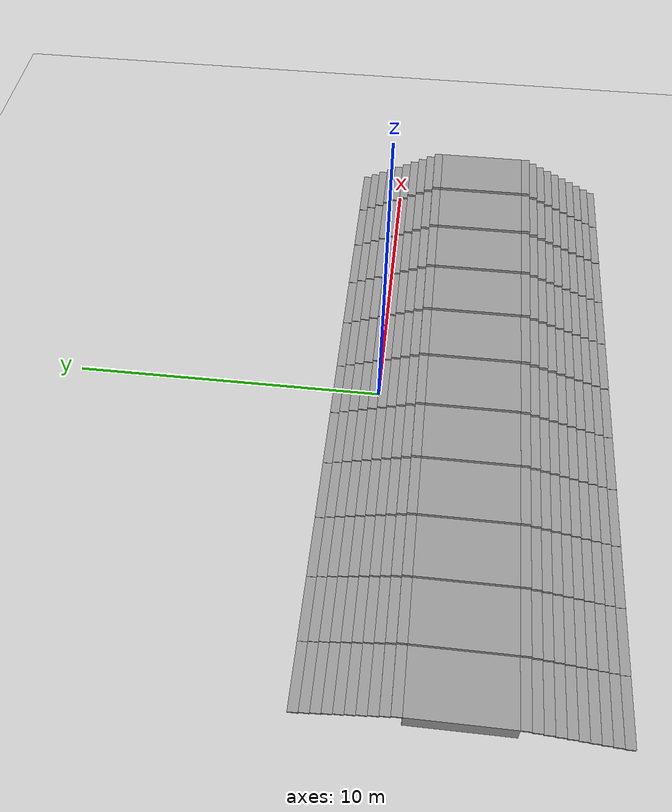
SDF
<sdf version="1.6">
 <world name="default">
  <light name="sun" type="directional">
   <pose>0 0 10 0 -0 0</pose>
   <diffuse>0.8 0.8 0.8 1</diffuse>
   <specular>0.2 0.2 0.2 1</specular>
   <attenuation>
    <range>1000</range>
    <constant>0.9</constant>
    <linear>0.01</linear>
    <quadratic>0.001</quadratic>
   </attenuation>
   <direction>-0.5 0.1 -0.9</direction>
  </light>
  <model name="ground_plane">
   <static>1</static>
   <link name="link">
    <collision name="collision">
     <geometry><plane><normal>0 0 1</normal><size>100 100</size></plane></geometry>
     <surface>
      <contact><collide_bitmask>65535</collide_bitmask></contact>
      <friction><ode><mu>100</mu><mu2>50</mu2></ode></friction>
     </surface>
    </collision>
    <visual name="visual">
     <cast_shadows>0</cast_shadows>
     <geometry><plane><normal>0 0 1</normal><size>100 100</size></plane></geometry>
     <material>
      <script><uri>file://media/materials/scripts/gazebo.material</uri><name>Gazebo/Grey</name></script>
     </material>
    </visual>
   </link>
  </model>
  <gravity>0 0 -9.8</gravity>
  <magnetic_field>6e-06 2.3e-05 -4.2e-05</magnetic_field>
  <atmosphere type="adiabatic"/>
  <physics name="default_physics" default="0" type="ode">
   <max_step_size>0.001</max_step_size>
   <real_time_factor>1</real_time_factor>
   <real_time_update_rate>1000</real_time_update_rate>
  </physics>
  <scene><ambient>0.4 0.4 0.4 1</ambient><background>0.7 0.7 0.7 1</background><shadows>1</shadows></scene>
  <audio><device>default</device></audio>
  <spherical_coordinates>
   <surface_model>EARTH_WGS84</surface_model>
   <latitude_deg>0</latitude_deg>
   <longitude_deg>0</longitude_deg>
   <elevation>0</elevation>
   <heading_deg>0</heading_deg>
  </spherical_coordinates>
  <model name="StairsWorld3">
   <pose>0 -3 0 0 -0 0</pose>
   <link name="Stairs_1">
    <visual name="Stairs_1_Visual_0">
     <pose>0 4.35 0.05 0 -0 0</pose>
     <geometry><box><size>2 0.3 0.1</size></box></geometry>
     <material>
      <script><uri>file://media/materials/scripts/gazebo.material</uri><name>Gazebo/Grey</name></script>
      <ambient>1 1 1 1</ambient>
     </material>
     <meta><layer>0</layer></meta>
    </visual>
    <collision name="Stairs_1_Collision_0">
     <geometry><box><size>2 0.3 0.1</size></box></geometry>
     <pose>0 4.35 0.05 0 -0 0</pose>
    </collision>
    <visual name="Stairs_1_Visual_1">
     <pose>0 4.05 0.15 0 -0 0</pose>
     <geometry><box><size>2 0.3 0.1</size></box></geometry>
     <material>
      <script><uri>file://media/materials/scripts/gazebo.material</uri><name>Gazebo/Grey</name></script>
      <ambient>1 1 1 1</ambient>
     </material>
     <meta><layer>0</layer></meta>
    </visual>
    <collision name="Stairs_1_Collision_1">
     <geometry><box><size>2 0.3 0.1</size></box></geometry>
     <pose>0 4.05 0.15 0 -0 0</pose>
    </collision>
    <visual name="Stairs_1_Visual_2">
     <pose>0 3.75 0.25 0 -0 0</pose>
     <geometry><box><size>2 0.3 0.1</size></box></geometry>
     <material>
      <script><uri>file://media/materials/scripts/gazebo.material</uri><name>Gazebo/Grey</name></script>
      <ambient>1 1 1 1</ambient>
     </material>
     <meta><layer>0</layer></meta>
    </visual>
    <collision name="Stairs_1_Collision_2">
     <geometry><box><size>2 0.3 0.1</size></box></geometry>
     <pose>0 3.75 0.25 0 -0 0</pose>
    </collision>
    <visual name="Stairs_1_Visual_3">
     <pose>0 3.45 0.35 0 -0 0</pose>
     <geometry><box><size>2 0.3 0.1</size></box></geometry>
     <material>
      <script><uri>file://media/materials/scripts/gazebo.material</uri><name>Gazebo/Grey</name></script>
      <ambient>1 1 1 1</ambient>
     </material>
     <meta><layer>0</layer></meta>
    </visual>
    <collision name="Stairs_1_Collision_3">
     <geometry><box><size>2 0.3 0.1</size></box></geometry>
     <pose>0 3.45 0.35 0 -0 0</pose>
    </collision>
    <visual name="Stairs_1_Visual_4">
     <pose>0 3.15 0.45 0 -0 0</pose>
     <geometry><box><size>2 0.3 0.1</size></box></geometry>
     <material>
      <script><uri>file://media/materials/scripts/gazebo.material</uri><name>Gazebo/Grey</name></script>
      <ambient>1 1 1 1</ambient>
     </material>
     <meta><layer>0</layer></meta>
    </visual>
    <collision name="Stairs_1_Collision_4">
     <geometry><box><size>2 0.3 0.1</size></box></geometry>
     <pose>0 3.15 0.45 0 -0 0</pose>
    </collision>
    <visual name="Stairs_1_Visual_5">
     <pose>0 2.85 0.55 0 -0 0</pose>
     <geometry><box><size>2 0.3 0.1</size></box></geometry>
     <material>
      <script><uri>file://media/materials/scripts/gazebo.material</uri><name>Gazebo/Grey</name></script>
      <ambient>1 1 1 1</ambient>
     </material>
     <meta><layer>0</layer></meta>
    </visual>
    <collision name="Stairs_1_Collision_5">
     <geometry><box><size>2 0.3 0.1</size></box></geometry>
     <pose>0 2.85 0.55 0 -0 0</pose>
    </collision>
    <visual name="Stairs_1_Visual_6">
     <pose>0 2.55 0.65 0 -0 0</pose>
     <geometry><box><size>2 0.3 0.1</size></box></geometry>
     <material>
      <script><uri>file://media/materials/scripts/gazebo.material</uri><name>Gazebo/Grey</name></script>
      <ambient>1 1 1 1</ambient>
     </material>
     <meta><layer>0</layer></meta>
    </visual>
    <collision name="Stairs_1_Collision_6">
     <geometry><box><size>2 0.3 0.1</size></box></geometry>
     <pose>0 2.55 0.65 0 -0 0</pose>
    </collision>
    <visual name="Stairs_1_Visual_7">
     <pose>0 2.25 0.75 0 -0 0</pose>
     <geometry><box><size>2 0.3 0.1</size></box></geometry>
     <material>
      <script><uri>file://media/materials/scripts/gazebo.material</uri><name>Gazebo/Grey</name></script>
      <ambient>1 1 1 1</ambient>
     </material>
     <meta><layer>0</layer></meta>
    </visual>
    <collision name="Stairs_1_Collision_7">
     <geometry><box><size>2 0.3 0.1</size></box></geometry>
     <pose>0 2.25 0.75 0 -0 0</pose>
    </collision>
    <visual name="Stairs_1_Visual_8">
     <pose>0 1.95 0.85 0 -0 0</pose>
     <geometry><box><size>2 0.3 0.1</size></box></geometry>
     <material>
      <script><uri>file://media/materials/scripts/gazebo.material</uri><name>Gazebo/Grey</name></script>
      <ambient>1 1 1 1</ambient>
     </material>
     <meta><layer>0</layer></meta>
    </visual>
    <collision name="Stairs_1_Collision_8">
     <geometry><box><size>2 0.3 0.1</size></box></geometry>
     <pose>0 1.95 0.85 0 -0 0</pose>
    </collision>
    <visual name="Stairs_1_Visual_9">
     <pose>0 1.65 0.95 0 -0 0</pose>
     <geometry><box><size>2 0.3 0.1</size></box></geometry>
     <material>
      <script><uri>file://media/materials/scripts/gazebo.material</uri><name>Gazebo/Grey</name></script>
      <ambient>1 1 1 1</ambient>
     </material>
     <meta><layer>0</layer></meta>
    </visual>
    <collision name="Stairs_1_Collision_9">
     <geometry><box><size>2 0.3 0.1</size></box></geometry>
     <pose>0 1.65 0.95 0 -0 0</pose>
    </collision>
   </link>
   <link name="Stairs_10">
    <visual name="Stairs_10_Visual_0">
     <pose>4 4.35 0.06 0 -0 0</pose>
     <geometry><box><size>2 0.3 0.12</size></box></geometry>
     <material>
      <script><uri>file://media/materials/scripts/gazebo.material</uri><name>Gazebo/Grey</name></script>
      <ambient>1 1 1 1</ambient>
     </material>
     <meta><layer>0</layer></meta>
    </visual>
    <collision name="Stairs_10_Collision_0">
     <geometry><box><size>2 0.3 0.12</size></box></geometry>
     <pose>4 4.35 0.06 0 -0 0</pose>
    </collision>
    <visual name="Stairs_10_Visual_1">
     <pose>4 4.05 0.18 0 -0 0</pose>
     <geometry><box><size>2 0.3 0.12</size></box></geometry>
     <material>
      <script><uri>file://media/materials/scripts/gazebo.material</uri><name>Gazebo/Grey</name></script>
      <ambient>1 1 1 1</ambient>
     </material>
     <meta><layer>0</layer></meta>
    </visual>
    <collision name="Stairs_10_Collision_1">
     <geometry><box><size>2 0.3 0.12</size></box></geometry>
     <pose>4 4.05 0.18 0 -0 0</pose>
    </collision>
    <visual name="Stairs_10_Visual_2">
     <pose>4 3.75 0.3 0 -0 0</pose>
     <geometry><box><size>2 0.3 0.12</size></box></geometry>
     <material>
      <script><uri>file://media/materials/scripts/gazebo.material</uri><name>Gazebo/Grey</name></script>
      <ambient>1 1 1 1</ambient>
     </material>
     <meta><layer>0</layer></meta>
    </visual>
    <collision name="Stairs_10_Collision_2">
     <geometry><box><size>2 0.3 0.12</size></box></geometry>
     <pose>4 3.75 0.3 0 -0 0</pose>
    </collision>
    <visual name="Stairs_10_Visual_3">
     <pose>4 3.45 0.42 0 -0 0</pose>
     <geometry><box><size>2 0.3 0.12</size></box></geometry>
     <material>
      <script><uri>file://media/materials/scripts/gazebo.material</uri><name>Gazebo/Grey</name></script>
      <ambient>1 1 1 1</ambient>
     </material>
     <meta><layer>0</layer></meta>
    </visual>
    <collision name="Stairs_10_Collision_3">
     <geometry><box><size>2 0.3 0.12</size></box></geometry>
     <pose>4 3.45 0.42 0 -0 0</pose>
    </collision>
    <visual name="Stairs_10_Visual_4">
     <pose>4 3.15 0.54 0 -0 0</pose>
     <geometry><box><size>2 0.3 0.12</size></box></geometry>
     <material>
      <script><uri>file://media/materials/scripts/gazebo.material</uri><name>Gazebo/Grey</name></script>
      <ambient>1 1 1 1</ambient>
     </material>
     <meta><layer>0</layer></meta>
    </visual>
    <collision name="Stairs_10_Collision_4">
     <geometry><box><size>2 0.3 0.12</size></box></geometry>
     <pose>4 3.15 0.54 0 -0 0</pose>
    </collision>
    <visual name="Stairs_10_Visual_5">
     <pose>4 2.85 0.66 0 -0 0</pose>
     <geometry><box><size>2 0.3 0.12</size></box></geometry>
     <material>
      <script><uri>file://media/materials/scripts/gazebo.material</uri><name>Gazebo/Grey</name></script>
      <ambient>1 1 1 1</ambient>
     </material>
     <meta><layer>0</layer></meta>
    </visual>
    <collision name="Stairs_10_Collision_5">
     <geometry><box><size>2 0.3 0.12</size></box></geometry>
     <pose>4 2.85 0.66 0 -0 0</pose>
    </collision>
    <visual name="Stairs_10_Visual_6">
     <pose>4 2.55 0.78 0 -0 0</pose>
     <geometry><box><size>2 0.3 0.12</size></box></geometry>
     <material>
      <script><uri>file://media/materials/scripts/gazebo.material</uri><name>Gazebo/Grey</name></script>
      <ambient>1 1 1 1</ambient>
     </material>
     <meta><layer>0</layer></meta>
    </visual>
    <collision name="Stairs_10_Collision_6">
     <geometry><box><size>2 0.3 0.12</size></box></geometry>
     <pose>4 2.55 0.78 0 -0 0</pose>
    </collision>
    <visual name="Stairs_10_Visual_7">
     <pose>4 2.25 0.9 0 -0 0</pose>
     <geometry><box><size>2 0.3 0.12</size></box></geometry>
     <material>
      <script><uri>file://media/materials/scripts/gazebo.material</uri><name>Gazebo/Grey</name></script>
      <ambient>1 1 1 1</ambient>
     </material>
     <meta><layer>0</layer></meta>
    </visual>
    <collision name="Stairs_10_Collision_7">
     <geometry><box><size>2 0.3 0.12</size></box></geometry>
     <pose>4 2.25 0.9 0 -0 0</pose>
    </collision>
    <visual name="Stairs_10_Visual_8">
     <pose>4 1.95 1.02 0 -0 0</pose>
     <geometry><box><size>2 0.3 0.12</size></box></geometry>
     <material>
      <script><uri>file://media/materials/scripts/gazebo.material</uri><name>Gazebo/Grey</name></script>
      <ambient>1 1 1 1</ambient>
     </material>
     <meta><layer>0</layer></meta>
    </visual>
    <collision name="Stairs_10_Collision_8">
     <geometry><box><size>2 0.3 0.12</size></box></geometry>
     <pose>4 1.95 1.02 0 -0 0</pose>
    </collision>
    <visual name="Stairs_10_Visual_9">
     <pose>4 1.65 1.14 0 -0 0</pose>
     <geometry><box><size>2 0.3 0.12</size></box></geometry>
     <material>
      <script><uri>file://media/materials/scripts/gazebo.material</uri><name>Gazebo/Grey</name></script>
      <ambient>1 1 1 1</ambient>
     </material>
     <meta><layer>0</layer></meta>
    </visual>
    <collision name="Stairs_10_Collision_9">
     <geometry><box><size>2 0.3 0.12</size></box></geometry>
     <pose>4 1.65 1.14 0 -0 0</pose>
    </collision>
   </link>
   <link name="Stairs_11">
    <visual name="Stairs_11_Visual_0">
     <pose>6 4.35 0.065 0 -0 0</pose>
     <geometry><box><size>2 0.3 0.13</size></box></geometry>
     <material>
      <script><uri>file://media/materials/scripts/gazebo.material</uri><name>Gazebo/Grey</name></script>
      <ambient>1 1 1 1</ambient>
     </material>
     <meta><layer>0</layer></meta>
    </visual>
    <collision name="Stairs_11_Collision_0">
     <geometry><box><size>2 0.3 0.13</size></box></geometry>
     <pose>6 4.35 0.065 0 -0 0</pose>
    </collision>
    <visual name="Stairs_11_Visual_1">
     <pose>6 4.05 0.195 0 -0 0</pose>
     <geometry><box><size>2 0.3 0.13</size></box></geometry>
     <material>
      <script><uri>file://media/materials/scripts/gazebo.material</uri><name>Gazebo/Grey</name></script>
      <ambient>1 1 1 1</ambient>
     </material>
     <meta><layer>0</layer></meta>
    </visual>
    <collision name="Stairs_11_Collision_1">
     <geometry><box><size>2 0.3 0.13</size></box></geometry>
     <pose>6 4.05 0.195 0 -0 0</pose>
    </collision>
    <visual name="Stairs_11_Visual_2">
     <pose>6 3.75 0.325 0 -0 0</pose>
     <geometry><box><size>2 0.3 0.13</size></box></geometry>
     <material>
      <script><uri>file://media/materials/scripts/gazebo.material</uri><name>Gazebo/Grey</name></script>
      <ambient>1 1 1 1</ambient>
     </material>
     <meta><layer>0</layer></meta>
    </visual>
    <collision name="Stairs_11_Collision_2">
     <geometry><box><size>2 0.3 0.13</size></box></geometry>
     <pose>6 3.75 0.325 0 -0 0</pose>
    </collision>
    <visual name="Stairs_11_Visual_3">
     <pose>6 3.45 0.455 0 -0 0</pose>
     <geometry><box><size>2 0.3 0.13</size></box></geometry>
     <material>
      <script><uri>file://media/materials/scripts/gazebo.material</uri><name>Gazebo/Grey</name></script>
      <ambient>1 1 1 1</ambient>
     </material>
     <meta><layer>0</layer></meta>
    </visual>
    <collision name="Stairs_11_Collision_3">
     <geometry><box><size>2 0.3 0.13</size></box></geometry>
     <pose>6 3.45 0.455 0 -0 0</pose>
    </collision>
    <visual name="Stairs_11_Visual_4">
     <pose>6 3.15 0.585 0 -0 0</pose>
     <geometry><box><size>2 0.3 0.13</size></box></geometry>
     <material>
      <script><uri>file://media/materials/scripts/gazebo.material</uri><name>Gazebo/Grey</name></script>
      <ambient>1 1 1 1</ambient>
     </material>
     <meta><layer>0</layer></meta>
    </visual>
    <collision name="Stairs_11_Collision_4">
     <geometry><box><size>2 0.3 0.13</size></box></geometry>
     <pose>6 3.15 0.585 0 -0 0</pose>
    </collision>
    <visual name="Stairs_11_Visual_5">
     <pose>6 2.85 0.715 0 -0 0</pose>
     <geometry><box><size>2 0.3 0.13</size></box></geometry>
     <material>
      <script><uri>file://media/materials/scripts/gazebo.material</uri><name>Gazebo/Grey</name></script>
      <ambient>1 1 1 1</ambient>
     </material>
     <meta><layer>0</layer></meta>
    </visual>
    <collision name="Stairs_11_Collision_5">
     <geometry><box><size>2 0.3 0.13</size></box></geometry>
     <pose>6 2.85 0.715 0 -0 0</pose>
    </collision>
    <visual name="Stairs_11_Visual_6">
     <pose>6 2.55 0.845 0 -0 0</pose>
     <geometry><box><size>2 0.3 0.13</size></box></geometry>
     <material>
      <script><uri>file://media/materials/scripts/gazebo.material</uri><name>Gazebo/Grey</name></script>
      <ambient>1 1 1 1</ambient>
     </material>
     <meta><layer>0</layer></meta>
    </visual>
    <collision name="Stairs_11_Collision_6">
     <geometry><box><size>2 0.3 0.13</size></box></geometry>
     <pose>6 2.55 0.845 0 -0 0</pose>
    </collision>
    <visual name="Stairs_11_Visual_7">
     <pose>6 2.25 0.975 0 -0 0</pose>
     <geometry><box><size>2 0.3 0.13</size></box></geometry>
     <material>
      <script><uri>file://media/materials/scripts/gazebo.material</uri><name>Gazebo/Grey</name></script>
      <ambient>1 1 1 1</ambient>
     </material>
     <meta><layer>0</layer></meta>
    </visual>
    <collision name="Stairs_11_Collision_7">
     <geometry><box><size>2 0.3 0.13</size></box></geometry>
     <pose>6 2.25 0.975 0 -0 0</pose>
    </collision>
    <visual name="Stairs_11_Visual_8">
     <pose>6 1.95 1.105 0 -0 0</pose>
     <geometry><box><size>2 0.3 0.13</size></box></geometry>
     <material>
      <script><uri>file://media/materials/scripts/gazebo.material</uri><name>Gazebo/Grey</name></script>
      <ambient>1 1 1 1</ambient>
     </material>
     <meta><layer>0</layer></meta>
    </visual>
    <collision name="Stairs_11_Collision_8">
     <geometry><box><size>2 0.3 0.13</size></box></geometry>
     <pose>6 1.95 1.105 0 -0 0</pose>
    </collision>
    <visual name="Stairs_11_Visual_9">
     <pose>6 1.65 1.235 0 -0 0</pose>
     <geometry><box><size>2 0.3 0.13</size></box></geometry>
     <material>
      <script><uri>file://media/materials/scripts/gazebo.material</uri><name>Gazebo/Grey</name></script>
      <ambient>1 1 1 1</ambient>
     </material>
     <meta><layer>0</layer></meta>
    </visual>
    <collision name="Stairs_11_Collision_9">
     <geometry><box><size>2 0.3 0.13</size></box></geometry>
     <pose>6 1.65 1.235 0 -0 0</pose>
    </collision>
   </link>
   <link name="Stairs_12">
    <visual name="Stairs_12_Visual_0">
     <pose>8 4.35 0.07 0 -0 0</pose>
     <geometry><box><size>2 0.3 0.14</size></box></geometry>
     <material>
      <script><uri>file://media/materials/scripts/gazebo.material</uri><name>Gazebo/Grey</name></script>
      <ambient>1 1 1 1</ambient>
     </material>
     <meta><layer>0</layer></meta>
    </visual>
    <collision name="Stairs_12_Collision_0">
     <geometry><box><size>2 0.3 0.14</size></box></geometry>
     <pose>8 4.35 0.07 0 -0 0</pose>
    </collision>
    <visual name="Stairs_12_Visual_1">
     <pose>8 4.05 0.21 0 -0 0</pose>
     <geometry><box><size>2 0.3 0.14</size></box></geometry>
     <material>
      <script><uri>file://media/materials/scripts/gazebo.material</uri><name>Gazebo/Grey</name></script>
      <ambient>1 1 1 1</ambient>
     </material>
     <meta><layer>0</layer></meta>
    </visual>
    <collision name="Stairs_12_Collision_1">
     <geometry><box><size>2 0.3 0.14</size></box></geometry>
     <pose>8 4.05 0.21 0 -0 0</pose>
    </collision>
    <visual name="Stairs_12_Visual_2">
     <pose>8 3.75 0.35 0 -0 0</pose>
     <geometry><box><size>2 0.3 0.14</size></box></geometry>
     <material>
      <script><uri>file://media/materials/scripts/gazebo.material</uri><name>Gazebo/Grey</name></script>
      <ambient>1 1 1 1</ambient>
     </material>
     <meta><layer>0</layer></meta>
    </visual>
    <collision name="Stairs_12_Collision_2">
     <geometry><box><size>2 0.3 0.14</size></box></geometry>
     <pose>8 3.75 0.35 0 -0 0</pose>
    </collision>
    <visual name="Stairs_12_Visual_3">
     <pose>8 3.45 0.49 0 -0 0</pose>
     <geometry><box><size>2 0.3 0.14</size></box></geometry>
     <material>
      <script><uri>file://media/materials/scripts/gazebo.material</uri><name>Gazebo/Grey</name></script>
      <ambient>1 1 1 1</ambient>
     </material>
     <meta><layer>0</layer></meta>
    </visual>
    <collision name="Stairs_12_Collision_3">
     <geometry><box><size>2 0.3 0.14</size></box></geometry>
     <pose>8 3.45 0.49 0 -0 0</pose>
    </collision>
    <visual name="Stairs_12_Visual_4">
     <pose>8 3.15 0.63 0 -0 0</pose>
     <geometry><box><size>2 0.3 0.14</size></box></geometry>
     <material>
      <script><uri>file://media/materials/scripts/gazebo.material</uri><name>Gazebo/Grey</name></script>
      <ambient>1 1 1 1</ambient>
     </material>
     <meta><layer>0</layer></meta>
    </visual>
    <collision name="Stairs_12_Collision_4">
     <geometry><box><size>2 0.3 0.14</size></box></geometry>
     <pose>8 3.15 0.63 0 -0 0</pose>
    </collision>
    <visual name="Stairs_12_Visual_5">
     <pose>8 2.85 0.77 0 -0 0</pose>
     <geometry><box><size>2 0.3 0.14</size></box></geometry>
     <material>
      <script><uri>file://media/materials/scripts/gazebo.material</uri><name>Gazebo/Grey</name></script>
      <ambient>1 1 1 1</ambient>
     </material>
     <meta><layer>0</layer></meta>
    </visual>
    <collision name="Stairs_12_Collision_5">
     <geometry><box><size>2 0.3 0.14</size></box></geometry>
     <pose>8 2.85 0.77 0 -0 0</pose>
    </collision>
    <visual name="Stairs_12_Visual_6">
     <pose>8 2.55 0.91 0 -0 0</pose>
     <geometry><box><size>2 0.3 0.14</size></box></geometry>
     <material>
      <script><uri>file://media/materials/scripts/gazebo.material</uri><name>Gazebo/Grey</name></script>
      <ambient>1 1 1 1</ambient>
     </material>
     <meta><layer>0</layer></meta>
    </visual>
    <collision name="Stairs_12_Collision_6">
     <geometry><box><size>2 0.3 0.14</size></box></geometry>
     <pose>8 2.55 0.91 0 -0 0</pose>
    </collision>
    <visual name="Stairs_12_Visual_7">
     <pose>8 2.25 1.05 0 -0 0</pose>
     <geometry><box><size>2 0.3 0.14</size></box></geometry>
     <material>
      <script><uri>file://media/materials/scripts/gazebo.material</uri><name>Gazebo/Grey</name></script>
      <ambient>1 1 1 1</ambient>
     </material>
     <meta><layer>0</layer></meta>
    </visual>
    <collision name="Stairs_12_Collision_7">
     <geometry><box><size>2 0.3 0.14</size></box></geometry>
     <pose>8 2.25 1.05 0 -0 0</pose>
    </collision>
    <visual name="Stairs_12_Visual_8">
     <pose>8 1.95 1.19 0 -0 0</pose>
     <geometry><box><size>2 0.3 0.14</size></box></geometry>
     <material>
      <script><uri>file://media/materials/scripts/gazebo.material</uri><name>Gazebo/Grey</name></script>
      <ambient>1 1 1 1</ambient>
     </material>
     <meta><layer>0</layer></meta>
    </visual>
    <collision name="Stairs_12_Collision_8">
     <geometry><box><size>2 0.3 0.14</size></box></geometry>
     <pose>8 1.95 1.19 0 -0 0</pose>
    </collision>
    <visual name="Stairs_12_Visual_9">
     <pose>8 1.65 1.33 0 -0 0</pose>
     <geometry><box><size>2 0.3 0.14</size></box></geometry>
     <material>
      <script><uri>file://media/materials/scripts/gazebo.material</uri><name>Gazebo/Grey</name></script>
      <ambient>1 1 1 1</ambient>
     </material>
     <meta><layer>0</layer></meta>
    </visual>
    <collision name="Stairs_12_Collision_9">
     <geometry><box><size>2 0.3 0.14</size></box></geometry>
     <pose>8 1.65 1.33 0 -0 0</pose>
    </collision>
   </link>
   <link name="Stairs_13">
    <visual name="Stairs_13_Visual_0">
     <pose>10 4.35 0.075 0 -0 0</pose>
     <geometry><box><size>2 0.3 0.15</size></box></geometry>
     <material>
      <script><uri>file://media/materials/scripts/gazebo.material</uri><name>Gazebo/Grey</name></script>
      <ambient>1 1 1 1</ambient>
     </material>
     <meta><layer>0</layer></meta>
    </visual>
    <collision name="Stairs_13_Collision_0">
     <geometry><box><size>2 0.3 0.15</size></box></geometry>
     <pose>10 4.35 0.075 0 -0 0</pose>
    </collision>
    <visual name="Stairs_13_Visual_1">
     <pose>10 4.05 0.225 0 -0 0</pose>
     <geometry><box><size>2 0.3 0.15</size></box></geometry>
     <material>
      <script><uri>file://media/materials/scripts/gazebo.material</uri><name>Gazebo/Grey</name></script>
      <ambient>1 1 1 1</ambient>
     </material>
     <meta><layer>0</layer></meta>
    </visual>
    <collision name="Stairs_13_Collision_1">
     <geometry><box><size>2 0.3 0.15</size></box></geometry>
     <pose>10 4.05 0.225 0 -0 0</pose>
    </collision>
    <visual name="Stairs_13_Visual_2">
     <pose>10 3.75 0.375 0 -0 0</pose>
     <geometry><box><size>2 0.3 0.15</size></box></geometry>
     <material>
      <script><uri>file://media/materials/scripts/gazebo.material</uri><name>Gazebo/Grey</name></script>
      <ambient>1 1 1 1</ambient>
     </material>
     <meta><layer>0</layer></meta>
    </visual>
    <collision name="Stairs_13_Collision_2">
     <geometry><box><size>2 0.3 0.15</size></box></geometry>
     <pose>10 3.75 0.375 0 -0 0</pose>
    </collision>
    <visual name="Stairs_13_Visual_3">
     <pose>10 3.45 0.525 0 -0 0</pose>
     <geometry><box><size>2 0.3 0.15</size></box></geometry>
     <material>
      <script><uri>file://media/materials/scripts/gazebo.material</uri><name>Gazebo/Grey</name></script>
      <ambient>1 1 1 1</ambient>
     </material>
     <meta><layer>0</layer></meta>
    </visual>
    <collision name="Stairs_13_Collision_3">
     <geometry><box><size>2 0.3 0.15</size></box></geometry>
     <pose>10 3.45 0.525 0 -0 0</pose>
    </collision>
    <visual name="Stairs_13_Visual_4">
     <pose>10 3.15 0.675 0 -0 0</pose>
     <geometry><box><size>2 0.3 0.15</size></box></geometry>
     <material>
      <script><uri>file://media/materials/scripts/gazebo.material</uri><name>Gazebo/Grey</name></script>
      <ambient>1 1 1 1</ambient>
     </material>
     <meta><layer>0</layer></meta>
    </visual>
    <collision name="Stairs_13_Collision_4">
     <geometry><box><size>2 0.3 0.15</size></box></geometry>
     <pose>10 3.15 0.675 0 -0 0</pose>
    </collision>
    <visual name="Stairs_13_Visual_5">
     <pose>10 2.85 0.825 0 -0 0</pose>
     <geometry><box><size>2 0.3 0.15</size></box></geometry>
     <material>
      <script><uri>file://media/materials/scripts/gazebo.material</uri><name>Gazebo/Grey</name></script>
      <ambient>1 1 1 1</ambient>
     </material>
     <meta><layer>0</layer></meta>
    </visual>
    <collision name="Stairs_13_Collision_5">
     <geometry><box><size>2 0.3 0.15</size></box></geometry>
     <pose>10 2.85 0.825 0 -0 0</pose>
    </collision>
    <visual name="Stairs_13_Visual_6">
     <pose>10 2.55 0.975 0 -0 0</pose>
     <geometry><box><size>2 0.3 0.15</size></box></geometry>
     <material>
      <script><uri>file://media/materials/scripts/gazebo.material</uri><name>Gazebo/Grey</name></script>
      <ambient>1 1 1 1</ambient>
     </material>
     <meta><layer>0</layer></meta>
    </visual>
    <collision name="Stairs_13_Collision_6">
     <geometry><box><size>2 0.3 0.15</size></box></geometry>
     <pose>10 2.55 0.975 0 -0 0</pose>
    </collision>
    <visual name="Stairs_13_Visual_7">
     <pose>10 2.25 1.125 0 -0 0</pose>
     <geometry><box><size>2 0.3 0.15</size></box></geometry>
     <material>
      <script><uri>file://media/materials/scripts/gazebo.material</uri><name>Gazebo/Grey</name></script>
      <ambient>1 1 1 1</ambient>
     </material>
     <meta><layer>0</layer></meta>
    </visual>
    <collision name="Stairs_13_Collision_7">
     <geometry><box><size>2 0.3 0.15</size></box></geometry>
     <pose>10 2.25 1.125 0 -0 0</pose>
    </collision>
    <visual name="Stairs_13_Visual_8">
     <pose>10 1.95 1.275 0 -0 0</pose>
     <geometry><box><size>2 0.3 0.15</size></box></geometry>
     <material>
      <script><uri>file://media/materials/scripts/gazebo.material</uri><name>Gazebo/Grey</name></script>
      <ambient>1 1 1 1</ambient>
     </material>
     <meta><layer>0</layer></meta>
    </visual>
    <collision name="Stairs_13_Collision_8">
     <geometry><box><size>2 0.3 0.15</size></box></geometry>
     <pose>10 1.95 1.275 0 -0 0</pose>
    </collision>
    <visual name="Stairs_13_Visual_9">
     <pose>10 1.65 1.425 0 -0 0</pose>
     <geometry><box><size>2 0.3 0.15</size></box></geometry>
     <material>
      <script><uri>file://media/materials/scripts/gazebo.material</uri><name>Gazebo/Grey</name></script>
      <ambient>1 1 1 1</ambient>
     </material>
     <meta><layer>0</layer></meta>
    </visual>
    <collision name="Stairs_13_Collision_9">
     <geometry><box><size>2 0.3 0.15</size></box></geometry>
     <pose>10 1.65 1.425 0 -0 0</pose>
    </collision>
   </link>
   <link name="Stairs_18">
    <visual name="Stairs_18_Visual_0">
     <pose>-0.020114 -4.35 0.05 0 0 -3.14159</pose>
     <geometry><box><size>2 0.3 0.1</size></box></geometry>
     <material>
      <script><uri>file://media/materials/scripts/gazebo.material</uri><name>Gazebo/Grey</name></script>
      <ambient>1 1 1 1</ambient>
     </material>
     <meta><layer>0</layer></meta>
    </visual>
    <collision name="Stairs_18_Collision_0">
     <geometry><box><size>2 0.3 0.1</size></box></geometry>
     <pose>-0.020114 -4.35 0.05 0 0 -3.14159</pose>
    </collision>
    <visual name="Stairs_18_Visual_1">
     <pose>-0.020114 -4.05 0.15 0 0 -3.14159</pose>
     <geometry><box><size>2 0.3 0.1</size></box></geometry>
     <material>
      <script><uri>file://media/materials/scripts/gazebo.material</uri><name>Gazebo/Grey</name></script>
      <ambient>1 1 1 1</ambient>
     </material>
     <meta><layer>0</layer></meta>
    </visual>
    <collision name="Stairs_18_Collision_1">
     <geometry><box><size>2 0.3 0.1</size></box></geometry>
     <pose>-0.020114 -4.05 0.15 0 0 -3.14159</pose>
    </collision>
    <visual name="Stairs_18_Visual_2">
     <pose>-0.020114 -3.75 0.25 0 0 -3.14159</pose>
     <geometry><box><size>2 0.3 0.1</size></box></geometry>
     <material>
      <script><uri>file://media/materials/scripts/gazebo.material</uri><name>Gazebo/Grey</name></script>
      <ambient>1 1 1 1</ambient>
     </material>
     <meta><layer>0</layer></meta>
    </visual>
    <collision name="Stairs_18_Collision_2">
     <geometry><box><size>2 0.3 0.1</size></box></geometry>
     <pose>-0.020114 -3.75 0.25 0 0 -3.14159</pose>
    </collision>
    <visual name="Stairs_18_Visual_3">
     <pose>-0.020114 -3.45 0.35 0 0 -3.14159</pose>
     <geometry><box><size>2 0.3 0.1</size></box></geometry>
     <material>
      <script><uri>file://media/materials/scripts/gazebo.material</uri><name>Gazebo/Grey</name></script>
      <ambient>1 1 1 1</ambient>
     </material>
     <meta><layer>0</layer></meta>
    </visual>
    <collision name="Stairs_18_Collision_3">
     <geometry><box><size>2 0.3 0.1</size></box></geometry>
     <pose>-0.020114 -3.45 0.35 0 0 -3.14159</pose>
    </collision>
    <visual name="Stairs_18_Visual_4">
     <pose>-0.020114 -3.15 0.45 0 0 -3.14159</pose>
     <geometry><box><size>2 0.3 0.1</size></box></geometry>
     <material>
      <script><uri>file://media/materials/scripts/gazebo.material</uri><name>Gazebo/Grey</name></script>
      <ambient>1 1 1 1</ambient>
     </material>
     <meta><layer>0</layer></meta>
    </visual>
    <collision name="Stairs_18_Collision_4">
     <geometry><box><size>2 0.3 0.1</size></box></geometry>
     <pose>-0.020114 -3.15 0.45 0 0 -3.14159</pose>
    </collision>
    <visual name="Stairs_18_Visual_5">
     <pose>-0.020114 -2.85 0.55 0 0 -3.14159</pose>
     <geometry><box><size>2 0.3 0.1</size></box></geometry>
     <material>
      <script><uri>file://media/materials/scripts/gazebo.material</uri><name>Gazebo/Grey</name></script>
      <ambient>1 1 1 1</ambient>
     </material>
     <meta><layer>0</layer></meta>
    </visual>
    <collision name="Stairs_18_Collision_5">
     <geometry><box><size>2 0.3 0.1</size></box></geometry>
     <pose>-0.020114 -2.85 0.55 0 0 -3.14159</pose>
    </collision>
    <visual name="Stairs_18_Visual_6">
     <pose>-0.020114 -2.55 0.65 0 0 -3.14159</pose>
     <geometry><box><size>2 0.3 0.1</size></box></geometry>
     <material>
      <script><uri>file://media/materials/scripts/gazebo.material</uri><name>Gazebo/Grey</name></script>
      <ambient>1 1 1 1</ambient>
     </material>
     <meta><layer>0</layer></meta>
    </visual>
    <collision name="Stairs_18_Collision_6">
     <geometry><box><size>2 0.3 0.1</size></box></geometry>
     <pose>-0.020114 -2.55 0.65 0 0 -3.14159</pose>
    </collision>
    <visual name="Stairs_18_Visual_7">
     <pose>-0.020114 -2.25 0.75 0 0 -3.14159</pose>
     <geometry><box><size>2 0.3 0.1</size></box></geometry>
     <material>
      <script><uri>file://media/materials/scripts/gazebo.material</uri><name>Gazebo/Grey</name></script>
      <ambient>1 1 1 1</ambient>
     </material>
     <meta><layer>0</layer></meta>
    </visual>
    <collision name="Stairs_18_Collision_7">
     <geometry><box><size>2 0.3 0.1</size></box></geometry>
     <pose>-0.020114 -2.25 0.75 0 0 -3.14159</pose>
    </collision>
    <visual name="Stairs_18_Visual_8">
     <pose>-0.020114 -1.95 0.85 0 0 -3.14159</pose>
     <geometry><box><size>2 0.3 0.1</size></box></geometry>
     <material>
      <script><uri>file://media/materials/scripts/gazebo.material</uri><name>Gazebo/Grey</name></script>
      <ambient>1 1 1 1</ambient>
     </material>
     <meta><layer>0</layer></meta>
    </visual>
    <collision name="Stairs_18_Collision_8">
     <geometry><box><size>2 0.3 0.1</size></box></geometry>
     <pose>-0.020114 -1.95 0.85 0 0 -3.14159</pose>
    </collision>
    <visual name="Stairs_18_Visual_9">
     <pose>-0.020114 -1.65 0.95 0 0 -3.14159</pose>
     <geometry><box><size>2 0.3 0.1</size></box></geometry>
     <material>
      <script><uri>file://media/materials/scripts/gazebo.material</uri><name>Gazebo/Grey</name></script>
      <ambient>1 1 1 1</ambient>
     </material>
     <meta><layer>0</layer></meta>
    </visual>
    <collision name="Stairs_18_Collision_9">
     <geometry><box><size>2 0.3 0.1</size></box></geometry>
     <pose>-0.020114 -1.65 0.95 0 0 -3.14159</pose>
    </collision>
   </link>
   <link name="Stairs_19">
    <visual name="Stairs_19_Visual_0">
     <pose>2 -4.35 0.055 0 0 -3.14159</pose>
     <geometry><box><size>2 0.3 0.11</size></box></geometry>
     <material>
      <script><uri>file://media/materials/scripts/gazebo.material</uri><name>Gazebo/Grey</name></script>
      <ambient>1 1 1 1</ambient>
     </material>
     <meta><layer>0</layer></meta>
    </visual>
    <collision name="Stairs_19_Collision_0">
     <geometry><box><size>2 0.3 0.11</size></box></geometry>
     <pose>2 -4.35 0.055 0 0 -3.14159</pose>
    </collision>
    <visual name="Stairs_19_Visual_1">
     <pose>2 -4.05 0.165 0 0 -3.14159</pose>
     <geometry><box><size>2 0.3 0.11</size></box></geometry>
     <material>
      <script><uri>file://media/materials/scripts/gazebo.material</uri><name>Gazebo/Grey</name></script>
      <ambient>1 1 1 1</ambient>
     </material>
     <meta><layer>0</layer></meta>
    </visual>
    <collision name="Stairs_19_Collision_1">
     <geometry><box><size>2 0.3 0.11</size></box></geometry>
     <pose>2 -4.05 0.165 0 0 -3.14159</pose>
    </collision>
    <visual name="Stairs_19_Visual_2">
     <pose>2 -3.75 0.275 0 0 -3.14159</pose>
     <geometry><box><size>2 0.3 0.11</size></box></geometry>
     <material>
      <script><uri>file://media/materials/scripts/gazebo.material</uri><name>Gazebo/Grey</name></script>
      <ambient>1 1 1 1</ambient>
     </material>
     <meta><layer>0</layer></meta>
    </visual>
    <collision name="Stairs_19_Collision_2">
     <geometry><box><size>2 0.3 0.11</size></box></geometry>
     <pose>2 -3.75 0.275 0 0 -3.14159</pose>
    </collision>
    <visual name="Stairs_19_Visual_3">
     <pose>2 -3.45 0.385 0 0 -3.14159</pose>
     <geometry><box><size>2 0.3 0.11</size></box></geometry>
     <material>
      <script><uri>file://media/materials/scripts/gazebo.material</uri><name>Gazebo/Grey</name></script>
      <ambient>1 1 1 1</ambient>
     </material>
     <meta><layer>0</layer></meta>
    </visual>
    <collision name="Stairs_19_Collision_3">
     <geometry><box><size>2 0.3 0.11</size></box></geometry>
     <pose>2 -3.45 0.385 0 0 -3.14159</pose>
    </collision>
    <visual name="Stairs_19_Visual_4">
     <pose>2 -3.15 0.495 0 0 -3.14159</pose>
     <geometry><box><size>2 0.3 0.11</size></box></geometry>
     <material>
      <script><uri>file://media/materials/scripts/gazebo.material</uri><name>Gazebo/Grey</name></script>
      <ambient>1 1 1 1</ambient>
     </material>
     <meta><layer>0</layer></meta>
    </visual>
    <collision name="Stairs_19_Collision_4">
     <geometry><box><size>2 0.3 0.11</size></box></geometry>
     <pose>2 -3.15 0.495 0 0 -3.14159</pose>
    </collision>
    <visual name="Stairs_19_Visual_5">
     <pose>2 -2.85 0.605 0 0 -3.14159</pose>
     <geometry><box><size>2 0.3 0.11</size></box></geometry>
     <material>
      <script><uri>file://media/materials/scripts/gazebo.material</uri><name>Gazebo/Grey</name></script>
      <ambient>1 1 1 1</ambient>
     </material>
     <meta><layer>0</layer></meta>
    </visual>
    <collision name="Stairs_19_Collision_5">
     <geometry><box><size>2 0.3 0.11</size></box></geometry>
     <pose>2 -2.85 0.605 0 0 -3.14159</pose>
    </collision>
    <visual name="Stairs_19_Visual_6">
     <pose>2 -2.55 0.715 0 0 -3.14159</pose>
     <geometry><box><size>2 0.3 0.11</size></box></geometry>
     <material>
      <script><uri>file://media/materials/scripts/gazebo.material</uri><name>Gazebo/Grey</name></script>
      <ambient>1 1 1 1</ambient>
     </material>
     <meta><layer>0</layer></meta>
    </visual>
    <collision name="Stairs_19_Collision_6">
     <geometry><box><size>2 0.3 0.11</size></box></geometry>
     <pose>2 -2.55 0.715 0 0 -3.14159</pose>
    </collision>
    <visual name="Stairs_19_Visual_7">
     <pose>2 -2.25 0.825 0 0 -3.14159</pose>
     <geometry><box><size>2 0.3 0.11</size></box></geometry>
     <material>
      <script><uri>file://media/materials/scripts/gazebo.material</uri><name>Gazebo/Grey</name></script>
      <ambient>1 1 1 1</ambient>
     </material>
     <meta><layer>0</layer></meta>
    </visual>
    <collision name="Stairs_19_Collision_7">
     <geometry><box><size>2 0.3 0.11</size></box></geometry>
     <pose>2 -2.25 0.825 0 0 -3.14159</pose>
    </collision>
    <visual name="Stairs_19_Visual_8">
     <pose>2 -1.95 0.935 0 0 -3.14159</pose>
     <geometry><box><size>2 0.3 0.11</size></box></geometry>
     <material>
      <script><uri>file://media/materials/scripts/gazebo.material</uri><name>Gazebo/Grey</name></script>
      <ambient>1 1 1 1</ambient>
     </material>
     <meta><layer>0</layer></meta>
    </visual>
    <collision name="Stairs_19_Collision_8">
     <geometry><box><size>2 0.3 0.11</size></box></geometry>
     <pose>2 -1.95 0.935 0 0 -3.14159</pose>
    </collision>
    <visual name="Stairs_19_Visual_9">
     <pose>2 -1.65 1.045 0 0 -3.14159</pose>
     <geometry><box><size>2 0.3 0.11</size></box></geometry>
     <material>
      <script><uri>file://media/materials/scripts/gazebo.material</uri><name>Gazebo/Grey</name></script>
      <ambient>1 1 1 1</ambient>
     </material>
     <meta><layer>0</layer></meta>
    </visual>
    <collision name="Stairs_19_Collision_9">
     <geometry><box><size>2 0.3 0.11</size></box></geometry>
     <pose>2 -1.65 1.045 0 0 -3.14159</pose>
    </collision>
   </link>
   <link name="Stairs_20">
    <visual name="Stairs_20_Visual_0">
     <pose>4 -4.35 0.06 0 0 -3.14159</pose>
     <geometry><box><size>2 0.3 0.12</size></box></geometry>
     <material>
      <script><uri>file://media/materials/scripts/gazebo.material</uri><name>Gazebo/Grey</name></script>
      <ambient>1 1 1 1</ambient>
     </material>
     <meta><layer>0</layer></meta>
    </visual>
    <collision name="Stairs_20_Collision_0">
     <geometry><box><size>2 0.3 0.12</size></box></geometry>
     <pose>4 -4.35 0.06 0 0 -3.14159</pose>
    </collision>
    <visual name="Stairs_20_Visual_1">
     <pose>4 -4.05 0.18 0 0 -3.14159</pose>
     <geometry><box><size>2 0.3 0.12</size></box></geometry>
     <material>
      <script><uri>file://media/materials/scripts/gazebo.material</uri><name>Gazebo/Grey</name></script>
      <ambient>1 1 1 1</ambient>
     </material>
     <meta><layer>0</layer></meta>
    </visual>
    <collision name="Stairs_20_Collision_1">
     <geometry><box><size>2 0.3 0.12</size></box></geometry>
     <pose>4 -4.05 0.18 0 0 -3.14159</pose>
    </collision>
    <visual name="Stairs_20_Visual_2">
     <pose>4 -3.75 0.3 0 0 -3.14159</pose>
     <geometry><box><size>2 0.3 0.12</size></box></geometry>
     <material>
      <script><uri>file://media/materials/scripts/gazebo.material</uri><name>Gazebo/Grey</name></script>
      <ambient>1 1 1 1</ambient>
     </material>
     <meta><layer>0</layer></meta>
    </visual>
    <collision name="Stairs_20_Collision_2">
     <geometry><box><size>2 0.3 0.12</size></box></geometry>
     <pose>4 -3.75 0.3 0 0 -3.14159</pose>
    </collision>
    <visual name="Stairs_20_Visual_3">
     <pose>4 -3.45 0.42 0 0 -3.14159</pose>
     <geometry><box><size>2 0.3 0.12</size></box></geometry>
     <material>
      <script><uri>file://media/materials/scripts/gazebo.material</uri><name>Gazebo/Grey</name></script>
      <ambient>1 1 1 1</ambient>
     </material>
     <meta><layer>0</layer></meta>
    </visual>
    <collision name="Stairs_20_Collision_3">
     <geometry><box><size>2 0.3 0.12</size></box></geometry>
     <pose>4 -3.45 0.42 0 0 -3.14159</pose>
    </collision>
    <visual name="Stairs_20_Visual_4">
     <pose>4 -3.15 0.54 0 0 -3.14159</pose>
     <geometry><box><size>2 0.3 0.12</size></box></geometry>
     <material>
      <script><uri>file://media/materials/scripts/gazebo.material</uri><name>Gazebo/Grey</name></script>
      <ambient>1 1 1 1</ambient>
     </material>
     <meta><layer>0</layer></meta>
    </visual>
    <collision name="Stairs_20_Collision_4">
     <geometry><box><size>2 0.3 0.12</size></box></geometry>
     <pose>4 -3.15 0.54 0 0 -3.14159</pose>
    </collision>
    <visual name="Stairs_20_Visual_5">
     <pose>4 -2.85 0.66 0 0 -3.14159</pose>
     <geometry><box><size>2 0.3 0.12</size></box></geometry>
     <material>
      <script><uri>file://media/materials/scripts/gazebo.material</uri><name>Gazebo/Grey</name></script>
      <ambient>1 1 1 1</ambient>
     </material>
     <meta><layer>0</layer></meta>
    </visual>
    <collision name="Stairs_20_Collision_5">
     <geometry><box><size>2 0.3 0.12</size></box></geometry>
     <pose>4 -2.85 0.66 0 0 -3.14159</pose>
    </collision>
    <visual name="Stairs_20_Visual_6">
     <pose>4 -2.55 0.78 0 0 -3.14159</pose>
     <geometry><box><size>2 0.3 0.12</size></box></geometry>
     <material>
      <script><uri>file://media/materials/scripts/gazebo.material</uri><name>Gazebo/Grey</name></script>
      <ambient>1 1 1 1</ambient>
     </material>
     <meta><layer>0</layer></meta>
    </visual>
    <collision name="Stairs_20_Collision_6">
     <geometry><box><size>2 0.3 0.12</size></box></geometry>
     <pose>4 -2.55 0.78 0 0 -3.14159</pose>
    </collision>
    <visual name="Stairs_20_Visual_7">
     <pose>4 -2.25 0.9 0 0 -3.14159</pose>
     <geometry><box><size>2 0.3 0.12</size></box></geometry>
     <material>
      <script><uri>file://media/materials/scripts/gazebo.material</uri><name>Gazebo/Grey</name></script>
      <ambient>1 1 1 1</ambient>
     </material>
     <meta><layer>0</layer></meta>
    </visual>
    <collision name="Stairs_20_Collision_7">
     <geometry><box><size>2 0.3 0.12</size></box></geometry>
     <pose>4 -2.25 0.9 0 0 -3.14159</pose>
    </collision>
    <visual name="Stairs_20_Visual_8">
     <pose>4 -1.95 1.02 0 0 -3.14159</pose>
     <geometry><box><size>2 0.3 0.12</size></box></geometry>
     <material>
      <script><uri>file://media/materials/scripts/gazebo.material</uri><name>Gazebo/Grey</name></script>
      <ambient>1 1 1 1</ambient>
     </material>
     <meta><layer>0</layer></meta>
    </visual>
    <collision name="Stairs_20_Collision_8">
     <geometry><box><size>2 0.3 0.12</size></box></geometry>
     <pose>4 -1.95 1.02 0 0 -3.14159</pose>
    </collision>
    <visual name="Stairs_20_Visual_9">
     <pose>4 -1.65 1.14 0 0 -3.14159</pose>
     <geometry><box><size>2 0.3 0.12</size></box></geometry>
     <material>
      <script><uri>file://media/materials/scripts/gazebo.material</uri><name>Gazebo/Grey</name></script>
      <ambient>1 1 1 1</ambient>
     </material>
     <meta><layer>0</layer></meta>
    </visual>
    <collision name="Stairs_20_Collision_9">
     <geometry><box><size>2 0.3 0.12</size></box></geometry>
     <pose>4 -1.65 1.14 0 0 -3.14159</pose>
    </collision>
   </link>
   <link name="Stairs_21">
    <visual name="Stairs_21_Visual_0">
     <pose>6 -4.35 0.065 0 0 -3.14159</pose>
     <geometry><box><size>2 0.3 0.13</size></box></geometry>
     <material>
      <script><uri>file://media/materials/scripts/gazebo.material</uri><name>Gazebo/Grey</name></script>
      <ambient>1 1 1 1</ambient>
     </material>
     <meta><layer>0</layer></meta>
    </visual>
    <collision name="Stairs_21_Collision_0">
     <geometry><box><size>2 0.3 0.13</size></box></geometry>
     <pose>6 -4.35 0.065 0 0 -3.14159</pose>
    </collision>
    <visual name="Stairs_21_Visual_1">
     <pose>6 -4.05 0.195 0 0 -3.14159</pose>
     <geometry><box><size>2 0.3 0.13</size></box></geometry>
     <material>
      <script><uri>file://media/materials/scripts/gazebo.material</uri><name>Gazebo/Grey</name></script>
      <ambient>1 1 1 1</ambient>
     </material>
     <meta><layer>0</layer></meta>
    </visual>
    <collision name="Stairs_21_Collision_1">
     <geometry><box><size>2 0.3 0.13</size></box></geometry>
     <pose>6 -4.05 0.195 0 0 -3.14159</pose>
    </collision>
    <visual name="Stairs_21_Visual_2">
     <pose>6 -3.75 0.325 0 0 -3.14159</pose>
     <geometry><box><size>2 0.3 0.13</size></box></geometry>
     <material>
      <script><uri>file://media/materials/scripts/gazebo.material</uri><name>Gazebo/Grey</name></script>
      <ambient>1 1 1 1</ambient>
     </material>
     <meta><layer>0</layer></meta>
    </visual>
    <collision name="Stairs_21_Collision_2">
     <geometry><box><size>2 0.3 0.13</size></box></geometry>
     <pose>6 -3.75 0.325 0 0 -3.14159</pose>
    </collision>
    <visual name="Stairs_21_Visual_3">
     <pose>6 -3.45 0.455 0 0 -3.14159</pose>
     <geometry><box><size>2 0.3 0.13</size></box></geometry>
     <material>
      <script><uri>file://media/materials/scripts/gazebo.material</uri><name>Gazebo/Grey</name></script>
      <ambient>1 1 1 1</ambient>
     </material>
     <meta><layer>0</layer></meta>
    </visual>
    <collision name="Stairs_21_Collision_3">
     <geometry><box><size>2 0.3 0.13</size></box></geometry>
     <pose>6 -3.45 0.455 0 0 -3.14159</pose>
    </collision>
    <visual name="Stairs_21_Visual_4">
     <pose>6 -3.15 0.585 0 0 -3.14159</pose>
     <geometry><box><size>2 0.3 0.13</size></box></geometry>
     <material>
      <script><uri>file://media/materials/scripts/gazebo.material</uri><name>Gazebo/Grey</name></script>
      <ambient>1 1 1 1</ambient>
     </material>
     <meta><layer>0</layer></meta>
    </visual>
    <collision name="Stairs_21_Collision_4">
     <geometry><box><size>2 0.3 0.13</size></box></geometry>
     <pose>6 -3.15 0.585 0 0 -3.14159</pose>
    </collision>
    <visual name="Stairs_21_Visual_5">
     <pose>6 -2.85 0.715 0 0 -3.14159</pose>
     <geometry><box><size>2 0.3 0.13</size></box></geometry>
     <material>
      <script><uri>file://media/materials/scripts/gazebo.material</uri><name>Gazebo/Grey</name></script>
      <ambient>1 1 1 1</ambient>
     </material>
     <meta><layer>0</layer></meta>
    </visual>
    <collision name="Stairs_21_Collision_5">
     <geometry><box><size>2 0.3 0.13</size></box></geometry>
     <pose>6 -2.85 0.715 0 0 -3.14159</pose>
    </collision>
    <visual name="Stairs_21_Visual_6">
     <pose>6 -2.55 0.845 0 0 -3.14159</pose>
     <geometry><box><size>2 0.3 0.13</size></box></geometry>
     <material>
      <script><uri>file://media/materials/scripts/gazebo.material</uri><name>Gazebo/Grey</name></script>
      <ambient>1 1 1 1</ambient>
     </material>
     <meta><layer>0</layer></meta>
    </visual>
    <collision name="Stairs_21_Collision_6">
     <geometry><box><size>2 0.3 0.13</size></box></geometry>
     <pose>6 -2.55 0.845 0 0 -3.14159</pose>
    </collision>
    <visual name="Stairs_21_Visual_7">
     <pose>6 -2.25 0.975 0 0 -3.14159</pose>
     <geometry><box><size>2 0.3 0.13</size></box></geometry>
     <material>
      <script><uri>file://media/materials/scripts/gazebo.material</uri><name>Gazebo/Grey</name></script>
      <ambient>1 1 1 1</ambient>
     </material>
     <meta><layer>0</layer></meta>
    </visual>
    <collision name="Stairs_21_Collision_7">
     <geometry><box><size>2 0.3 0.13</size></box></geometry>
     <pose>6 -2.25 0.975 0 0 -3.14159</pose>
    </collision>
    <visual name="Stairs_21_Visual_8">
     <pose>6 -1.95 1.105 0 0 -3.14159</pose>
     <geometry><box><size>2 0.3 0.13</size></box></geometry>
     <material>
      <script><uri>file://media/materials/scripts/gazebo.material</uri><name>Gazebo/Grey</name></script>
      <ambient>1 1 1 1</ambient>
     </material>
     <meta><layer>0</layer></meta>
    </visual>
    <collision name="Stairs_21_Collision_8">
     <geometry><box><size>2 0.3 0.13</size></box></geometry>
     <pose>6 -1.95 1.105 0 0 -3.14159</pose>
    </collision>
    <visual name="Stairs_21_Visual_9">
     <pose>6 -1.65 1.235 0 0 -3.14159</pose>
     <geometry><box><size>2 0.3 0.13</size></box></geometry>
     <material>
      <script><uri>file://media/materials/scripts/gazebo.material</uri><name>Gazebo/Grey</name></script>
      <ambient>1 1 1 1</ambient>
     </material>
     <meta><layer>0</layer></meta>
    </visual>
    <collision name="Stairs_21_Collision_9">
     <geometry><box><size>2 0.3 0.13</size></box></geometry>
     <pose>6 -1.65 1.235 0 0 -3.14159</pose>
    </collision>
   </link>
   <link name="Stairs_24">
    <visual name="Stairs_24_Visual_0">
     <pose>8.02011 -4.35 0.07 0 -0 -3.14159</pose>
     <geometry><box><size>2 0.3 0.14</size></box></geometry>
     <material>
      <script><uri>file://media/materials/scripts/gazebo.material</uri><name>Gazebo/Grey</name></script>
      <ambient>1 1 1 1</ambient>
     </material>
     <meta><layer>0</layer></meta>
    </visual>
    <collision name="Stairs_24_Collision_0">
     <geometry><box><size>2 0.3 0.14</size></box></geometry>
     <pose>8.02011 -4.35 0.07 0 -0 -3.14159</pose>
    </collision>
    <visual name="Stairs_24_Visual_1">
     <pose>8.02011 -4.05 0.21 0 -0 -3.14159</pose>
     <geometry><box><size>2 0.3 0.14</size></box></geometry>
     <material>
      <script><uri>file://media/materials/scripts/gazebo.material</uri><name>Gazebo/Grey</name></script>
      <ambient>1 1 1 1</ambient>
     </material>
     <meta><layer>0</layer></meta>
    </visual>
    <collision name="Stairs_24_Collision_1">
     <geometry><box><size>2 0.3 0.14</size></box></geometry>
     <pose>8.02011 -4.05 0.21 0 -0 -3.14159</pose>
    </collision>
    <visual name="Stairs_24_Visual_2">
     <pose>8.02011 -3.75 0.35 0 -0 -3.14159</pose>
     <geometry><box><size>2 0.3 0.14</size></box></geometry>
     <material>
      <script><uri>file://media/materials/scripts/gazebo.material</uri><name>Gazebo/Grey</name></script>
      <ambient>1 1 1 1</ambient>
     </material>
     <meta><layer>0</layer></meta>
    </visual>
    <collision name="Stairs_24_Collision_2">
     <geometry><box><size>2 0.3 0.14</size></box></geometry>
     <pose>8.02011 -3.75 0.35 0 -0 -3.14159</pose>
    </collision>
    <visual name="Stairs_24_Visual_3">
     <pose>8.02011 -3.45 0.49 0 -0 -3.14159</pose>
     <geometry><box><size>2 0.3 0.14</size></box></geometry>
     <material>
      <script><uri>file://media/materials/scripts/gazebo.material</uri><name>Gazebo/Grey</name></script>
      <ambient>1 1 1 1</ambient>
     </material>
     <meta><layer>0</layer></meta>
    </visual>
    <collision name="Stairs_24_Collision_3">
     <geometry><box><size>2 0.3 0.14</size></box></geometry>
     <pose>8.02011 -3.45 0.49 0 -0 -3.14159</pose>
    </collision>
    <visual name="Stairs_24_Visual_4">
     <pose>8.02011 -3.15 0.63 0 -0 -3.14159</pose>
     <geometry><box><size>2 0.3 0.14</size></box></geometry>
     <material>
      <script><uri>file://media/materials/scripts/gazebo.material</uri><name>Gazebo/Grey</name></script>
      <ambient>1 1 1 1</ambient>
     </material>
     <meta><layer>0</layer></meta>
    </visual>
    <collision name="Stairs_24_Collision_4">
     <geometry><box><size>2 0.3 0.14</size></box></geometry>
     <pose>8.02011 -3.15 0.63 0 -0 -3.14159</pose>
    </collision>
    <visual name="Stairs_24_Visual_5">
     <pose>8.02011 -2.85 0.77 0 -0 -3.14159</pose>
     <geometry><box><size>2 0.3 0.14</size></box></geometry>
     <material>
      <script><uri>file://media/materials/scripts/gazebo.material</uri><name>Gazebo/Grey</name></script>
      <ambient>1 1 1 1</ambient>
     </material>
     <meta><layer>0</layer></meta>
    </visual>
    <collision name="Stairs_24_Collision_5">
     <geometry><box><size>2 0.3 0.14</size></box></geometry>
     <pose>8.02011 -2.85 0.77 0 -0 -3.14159</pose>
    </collision>
    <visual name="Stairs_24_Visual_6">
     <pose>8.02011 -2.55 0.91 0 -0 -3.14159</pose>
     <geometry><box><size>2 0.3 0.14</size></box></geometry>
     <material>
      <script><uri>file://media/materials/scripts/gazebo.material</uri><name>Gazebo/Grey</name></script>
      <ambient>1 1 1 1</ambient>
     </material>
     <meta><layer>0</layer></meta>
    </visual>
    <collision name="Stairs_24_Collision_6">
     <geometry><box><size>2 0.3 0.14</size></box></geometry>
     <pose>8.02011 -2.55 0.91 0 -0 -3.14159</pose>
    </collision>
    <visual name="Stairs_24_Visual_7">
     <pose>8.02011 -2.25 1.05 0 -0 -3.14159</pose>
     <geometry><box><size>2 0.3 0.14</size></box></geometry>
     <material>
      <script><uri>file://media/materials/scripts/gazebo.material</uri><name>Gazebo/Grey</name></script>
      <ambient>1 1 1 1</ambient>
     </material>
     <meta><layer>0</layer></meta>
    </visual>
    <collision name="Stairs_24_Collision_7">
     <geometry><box><size>2 0.3 0.14</size></box></geometry>
     <pose>8.02011 -2.25 1.05 0 -0 -3.14159</pose>
    </collision>
    <visual name="Stairs_24_Visual_8">
     <pose>8.02011 -1.95 1.19 0 -0 -3.14159</pose>
     <geometry><box><size>2 0.3 0.14</size></box></geometry>
     <material>
      <script><uri>file://media/materials/scripts/gazebo.material</uri><name>Gazebo/Grey</name></script>
      <ambient>1 1 1 1</ambient>
     </material>
     <meta><layer>0</layer></meta>
    </visual>
    <collision name="Stairs_24_Collision_8">
     <geometry><box><size>2 0.3 0.14</size></box></geometry>
     <pose>8.02011 -1.95 1.19 0 -0 -3.14159</pose>
    </collision>
    <visual name="Stairs_24_Visual_9">
     <pose>8.02011 -1.65 1.33 0 -0 -3.14159</pose>
     <geometry><box><size>2 0.3 0.14</size></box></geometry>
     <material>
      <script><uri>file://media/materials/scripts/gazebo.material</uri><name>Gazebo/Grey</name></script>
      <ambient>1 1 1 1</ambient>
     </material>
     <meta><layer>0</layer></meta>
    </visual>
    <collision name="Stairs_24_Collision_9">
     <geometry><box><size>2 0.3 0.14</size></box></geometry>
     <pose>8.02011 -1.65 1.33 0 -0 -3.14159</pose>
    </collision>
   </link>
   <link name="Stairs_25">
    <visual name="Stairs_25_Visual_0">
     <pose>10 -4.35 0.075 0 0 -3.14159</pose>
     <geometry><box><size>2 0.3 0.15</size></box></geometry>
     <material>
      <script><uri>file://media/materials/scripts/gazebo.material</uri><name>Gazebo/Grey</name></script>
      <ambient>1 1 1 1</ambient>
     </material>
     <meta><layer>0</layer></meta>
    </visual>
    <collision name="Stairs_25_Collision_0">
     <geometry><box><size>2 0.3 0.15</size></box></geometry>
     <pose>10 -4.35 0.075 0 0 -3.14159</pose>
    </collision>
    <visual name="Stairs_25_Visual_1">
     <pose>10 -4.05 0.225 0 0 -3.14159</pose>
     <geometry><box><size>2 0.3 0.15</size></box></geometry>
     <material>
      <script><uri>file://media/materials/scripts/gazebo.material</uri><name>Gazebo/Grey</name></script>
      <ambient>1 1 1 1</ambient>
     </material>
     <meta><layer>0</layer></meta>
    </visual>
    <collision name="Stairs_25_Collision_1">
     <geometry><box><size>2 0.3 0.15</size></box></geometry>
     <pose>10 -4.05 0.225 0 0 -3.14159</pose>
    </collision>
    <visual name="Stairs_25_Visual_2">
     <pose>10 -3.75 0.375 0 0 -3.14159</pose>
     <geometry><box><size>2 0.3 0.15</size></box></geometry>
     <material>
      <script><uri>file://media/materials/scripts/gazebo.material</uri><name>Gazebo/Grey</name></script>
      <ambient>1 1 1 1</ambient>
     </material>
     <meta><layer>0</layer></meta>
    </visual>
    <collision name="Stairs_25_Collision_2">
     <geometry><box><size>2 0.3 0.15</size></box></geometry>
     <pose>10 -3.75 0.375 0 0 -3.14159</pose>
    </collision>
    <visual name="Stairs_25_Visual_3">
     <pose>10 -3.45 0.525 0 0 -3.14159</pose>
     <geometry><box><size>2 0.3 0.15</size></box></geometry>
     <material>
      <script><uri>file://media/materials/scripts/gazebo.material</uri><name>Gazebo/Grey</name></script>
      <ambient>1 1 1 1</ambient>
     </material>
     <meta><layer>0</layer></meta>
    </visual>
    <collision name="Stairs_25_Collision_3">
     <geometry><box><size>2 0.3 0.15</size></box></geometry>
     <pose>10 -3.45 0.525 0 0 -3.14159</pose>
    </collision>
    <visual name="Stairs_25_Visual_4">
     <pose>10 -3.15 0.675 0 0 -3.14159</pose>
     <geometry><box><size>2 0.3 0.15</size></box></geometry>
     <material>
      <script><uri>file://media/materials/scripts/gazebo.material</uri><name>Gazebo/Grey</name></script>
      <ambient>1 1 1 1</ambient>
     </material>
     <meta><layer>0</layer></meta>
    </visual>
    <collision name="Stairs_25_Collision_4">
     <geometry><box><size>2 0.3 0.15</size></box></geometry>
     <pose>10 -3.15 0.675 0 0 -3.14159</pose>
    </collision>
    <visual name="Stairs_25_Visual_5">
     <pose>10 -2.85 0.825 0 0 -3.14159</pose>
     <geometry><box><size>2 0.3 0.15</size></box></geometry>
     <material>
      <script><uri>file://media/materials/scripts/gazebo.material</uri><name>Gazebo/Grey</name></script>
      <ambient>1 1 1 1</ambient>
     </material>
     <meta><layer>0</layer></meta>
    </visual>
    <collision name="Stairs_25_Collision_5">
     <geometry><box><size>2 0.3 0.15</size></box></geometry>
     <pose>10 -2.85 0.825 0 0 -3.14159</pose>
    </collision>
    <visual name="Stairs_25_Visual_6">
     <pose>10 -2.55 0.975 0 0 -3.14159</pose>
     <geometry><box><size>2 0.3 0.15</size></box></geometry>
     <material>
      <script><uri>file://media/materials/scripts/gazebo.material</uri><name>Gazebo/Grey</name></script>
      <ambient>1 1 1 1</ambient>
     </material>
     <meta><layer>0</layer></meta>
    </visual>
    <collision name="Stairs_25_Collision_6">
     <geometry><box><size>2 0.3 0.15</size></box></geometry>
     <pose>10 -2.55 0.975 0 0 -3.14159</pose>
    </collision>
    <visual name="Stairs_25_Visual_7">
     <pose>10 -2.25 1.125 0 0 -3.14159</pose>
     <geometry><box><size>2 0.3 0.15</size></box></geometry>
     <material>
      <script><uri>file://media/materials/scripts/gazebo.material</uri><name>Gazebo/Grey</name></script>
      <ambient>1 1 1 1</ambient>
     </material>
     <meta><layer>0</layer></meta>
    </visual>
    <collision name="Stairs_25_Collision_7">
     <geometry><box><size>2 0.3 0.15</size></box></geometry>
     <pose>10 -2.25 1.125 0 0 -3.14159</pose>
    </collision>
    <visual name="Stairs_25_Visual_8">
     <pose>10 -1.95 1.275 0 0 -3.14159</pose>
     <geometry><box><size>2 0.3 0.15</size></box></geometry>
     <material>
      <script><uri>file://media/materials/scripts/gazebo.material</uri><name>Gazebo/Grey</name></script>
      <ambient>1 1 1 1</ambient>
     </material>
     <meta><layer>0</layer></meta>
    </visual>
    <collision name="Stairs_25_Collision_8">
     <geometry><box><size>2 0.3 0.15</size></box></geometry>
     <pose>10 -1.95 1.275 0 0 -3.14159</pose>
    </collision>
    <visual name="Stairs_25_Visual_9">
     <pose>10 -1.65 1.425 0 0 -3.14159</pose>
     <geometry><box><size>2 0.3 0.15</size></box></geometry>
     <material>
      <script><uri>file://media/materials/scripts/gazebo.material</uri><name>Gazebo/Grey</name></script>
      <ambient>1 1 1 1</ambient>
     </material>
     <meta><layer>0</layer></meta>
    </visual>
    <collision name="Stairs_25_Collision_9">
     <geometry><box><size>2 0.3 0.15</size></box></geometry>
     <pose>10 -1.65 1.425 0 0 -3.14159</pose>
    </collision>
   </link>
   <link name="Stairs_29">
    <visual name="Stairs_29_Visual_0">
     <pose>-2 4.35 0.045 0 -0 0</pose>
     <geometry><box><size>2 0.3 0.09</size></box></geometry>
     <material>
      <script><uri>file://media/materials/scripts/gazebo.material</uri><name>Gazebo/Grey</name></script>
      <ambient>1 1 1 1</ambient>
     </material>
     <meta><layer>0</layer></meta>
    </visual>
    <collision name="Stairs_29_Collision_0">
     <geometry><box><size>2 0.3 0.09</size></box></geometry>
     <pose>-2 4.35 0.045 0 -0 0</pose>
    </collision>
    <visual name="Stairs_29_Visual_1">
     <pose>-2 4.05 0.135 0 -0 0</pose>
     <geometry><box><size>2 0.3 0.09</size></box></geometry>
     <material>
      <script><uri>file://media/materials/scripts/gazebo.material</uri><name>Gazebo/Grey</name></script>
      <ambient>1 1 1 1</ambient>
     </material>
     <meta><layer>0</layer></meta>
    </visual>
    <collision name="Stairs_29_Collision_1">
     <geometry><box><size>2 0.3 0.09</size></box></geometry>
     <pose>-2 4.05 0.135 0 -0 0</pose>
    </collision>
    <visual name="Stairs_29_Visual_2">
     <pose>-2 3.75 0.225 0 -0 0</pose>
     <geometry><box><size>2 0.3 0.09</size></box></geometry>
     <material>
      <script><uri>file://media/materials/scripts/gazebo.material</uri><name>Gazebo/Grey</name></script>
      <ambient>1 1 1 1</ambient>
     </material>
     <meta><layer>0</layer></meta>
    </visual>
    <collision name="Stairs_29_Collision_2">
     <geometry><box><size>2 0.3 0.09</size></box></geometry>
     <pose>-2 3.75 0.225 0 -0 0</pose>
    </collision>
    <visual name="Stairs_29_Visual_3">
     <pose>-2 3.45 0.315 0 -0 0</pose>
     <geometry><box><size>2 0.3 0.09</size></box></geometry>
     <material>
      <script><uri>file://media/materials/scripts/gazebo.material</uri><name>Gazebo/Grey</name></script>
      <ambient>1 1 1 1</ambient>
     </material>
     <meta><layer>0</layer></meta>
    </visual>
    <collision name="Stairs_29_Collision_3">
     <geometry><box><size>2 0.3 0.09</size></box></geometry>
     <pose>-2 3.45 0.315 0 -0 0</pose>
    </collision>
    <visual name="Stairs_29_Visual_4">
     <pose>-2 3.15 0.405 0 -0 0</pose>
     <geometry><box><size>2 0.3 0.09</size></box></geometry>
     <material>
      <script><uri>file://media/materials/scripts/gazebo.material</uri><name>Gazebo/Grey</name></script>
      <ambient>1 1 1 1</ambient>
     </material>
     <meta><layer>0</layer></meta>
    </visual>
    <collision name="Stairs_29_Collision_4">
     <geometry><box><size>2 0.3 0.09</size></box></geometry>
     <pose>-2 3.15 0.405 0 -0 0</pose>
    </collision>
    <visual name="Stairs_29_Visual_5">
     <pose>-2 2.85 0.495 0 -0 0</pose>
     <geometry><box><size>2 0.3 0.09</size></box></geometry>
     <material>
      <script><uri>file://media/materials/scripts/gazebo.material</uri><name>Gazebo/Grey</name></script>
      <ambient>1 1 1 1</ambient>
     </material>
     <meta><layer>0</layer></meta>
    </visual>
    <collision name="Stairs_29_Collision_5">
     <geometry><box><size>2 0.3 0.09</size></box></geometry>
     <pose>-2 2.85 0.495 0 -0 0</pose>
    </collision>
    <visual name="Stairs_29_Visual_6">
     <pose>-2 2.55 0.585 0 -0 0</pose>
     <geometry><box><size>2 0.3 0.09</size></box></geometry>
     <material>
      <script><uri>file://media/materials/scripts/gazebo.material</uri><name>Gazebo/Grey</name></script>
      <ambient>1 1 1 1</ambient>
     </material>
     <meta><layer>0</layer></meta>
    </visual>
    <collision name="Stairs_29_Collision_6">
     <geometry><box><size>2 0.3 0.09</size></box></geometry>
     <pose>-2 2.55 0.585 0 -0 0</pose>
    </collision>
    <visual name="Stairs_29_Visual_7">
     <pose>-2 2.25 0.675 0 -0 0</pose>
     <geometry><box><size>2 0.3 0.09</size></box></geometry>
     <material>
      <script><uri>file://media/materials/scripts/gazebo.material</uri><name>Gazebo/Grey</name></script>
      <ambient>1 1 1 1</ambient>
     </material>
     <meta><layer>0</layer></meta>
    </visual>
    <collision name="Stairs_29_Collision_7">
     <geometry><box><size>2 0.3 0.09</size></box></geometry>
     <pose>-2 2.25 0.675 0 -0 0</pose>
    </collision>
    <visual name="Stairs_29_Visual_8">
     <pose>-2 1.95 0.765 0 -0 0</pose>
     <geometry><box><size>2 0.3 0.09</size></box></geometry>
     <material>
      <script><uri>file://media/materials/scripts/gazebo.material</uri><name>Gazebo/Grey</name></script>
      <ambient>1 1 1 1</ambient>
     </material>
     <meta><layer>0</layer></meta>
    </visual>
    <collision name="Stairs_29_Collision_8">
     <geometry><box><size>2 0.3 0.09</size></box></geometry>
     <pose>-2 1.95 0.765 0 -0 0</pose>
    </collision>
    <visual name="Stairs_29_Visual_9">
     <pose>-2 1.65 0.855 0 -0 0</pose>
     <geometry><box><size>2 0.3 0.09</size></box></geometry>
     <material>
      <script><uri>file://media/materials/scripts/gazebo.material</uri><name>Gazebo/Grey</name></script>
      <ambient>1 1 1 1</ambient>
     </material>
     <meta><layer>0</layer></meta>
    </visual>
    <collision name="Stairs_29_Collision_9">
     <geometry><box><size>2 0.3 0.09</size></box></geometry>
     <pose>-2 1.65 0.855 0 -0 0</pose>
    </collision>
   </link>
   <link name="Stairs_30">
    <visual name="Stairs_30_Visual_0">
     <pose>-4 4.35 0.04 0 -0 0</pose>
     <geometry><box><size>2 0.3 0.08</size></box></geometry>
     <material>
      <script><uri>file://media/materials/scripts/gazebo.material</uri><name>Gazebo/Grey</name></script>
      <ambient>1 1 1 1</ambient>
     </material>
     <meta><layer>0</layer></meta>
    </visual>
    <collision name="Stairs_30_Collision_0">
     <geometry><box><size>2 0.3 0.08</size></box></geometry>
     <pose>-4 4.35 0.04 0 -0 0</pose>
    </collision>
    <visual name="Stairs_30_Visual_1">
     <pose>-4 4.05 0.12 0 -0 0</pose>
     <geometry><box><size>2 0.3 0.08</size></box></geometry>
     <material>
      <script><uri>file://media/materials/scripts/gazebo.material</uri><name>Gazebo/Grey</name></script>
      <ambient>1 1 1 1</ambient>
     </material>
     <meta><layer>0</layer></meta>
    </visual>
    <collision name="Stairs_30_Collision_1">
     <geometry><box><size>2 0.3 0.08</size></box></geometry>
     <pose>-4 4.05 0.12 0 -0 0</pose>
    </collision>
    <visual name="Stairs_30_Visual_2">
     <pose>-4 3.75 0.2 0 -0 0</pose>
     <geometry><box><size>2 0.3 0.08</size></box></geometry>
     <material>
      <script><uri>file://media/materials/scripts/gazebo.material</uri><name>Gazebo/Grey</name></script>
      <ambient>1 1 1 1</ambient>
     </material>
     <meta><layer>0</layer></meta>
    </visual>
    <collision name="Stairs_30_Collision_2">
     <geometry><box><size>2 0.3 0.08</size></box></geometry>
     <pose>-4 3.75 0.2 0 -0 0</pose>
    </collision>
    <visual name="Stairs_30_Visual_3">
     <pose>-4 3.45 0.28 0 -0 0</pose>
     <geometry><box><size>2 0.3 0.08</size></box></geometry>
     <material>
      <script><uri>file://media/materials/scripts/gazebo.material</uri><name>Gazebo/Grey</name></script>
      <ambient>1 1 1 1</ambient>
     </material>
     <meta><layer>0</layer></meta>
    </visual>
    <collision name="Stairs_30_Collision_3">
     <geometry><box><size>2 0.3 0.08</size></box></geometry>
     <pose>-4 3.45 0.28 0 -0 0</pose>
    </collision>
    <visual name="Stairs_30_Visual_4">
     <pose>-4 3.15 0.36 0 -0 0</pose>
     <geometry><box><size>2 0.3 0.08</size></box></geometry>
     <material>
      <script><uri>file://media/materials/scripts/gazebo.material</uri><name>Gazebo/Grey</name></script>
      <ambient>1 1 1 1</ambient>
     </material>
     <meta><layer>0</layer></meta>
    </visual>
    <collision name="Stairs_30_Collision_4">
     <geometry><box><size>2 0.3 0.08</size></box></geometry>
     <pose>-4 3.15 0.36 0 -0 0</pose>
    </collision>
    <visual name="Stairs_30_Visual_5">
     <pose>-4 2.85 0.44 0 -0 0</pose>
     <geometry><box><size>2 0.3 0.08</size></box></geometry>
     <material>
      <script><uri>file://media/materials/scripts/gazebo.material</uri><name>Gazebo/Grey</name></script>
      <ambient>1 1 1 1</ambient>
     </material>
     <meta><layer>0</layer></meta>
    </visual>
    <collision name="Stairs_30_Collision_5">
     <geometry><box><size>2 0.3 0.08</size></box></geometry>
     <pose>-4 2.85 0.44 0 -0 0</pose>
    </collision>
    <visual name="Stairs_30_Visual_6">
     <pose>-4 2.55 0.52 0 -0 0</pose>
     <geometry><box><size>2 0.3 0.08</size></box></geometry>
     <material>
      <script><uri>file://media/materials/scripts/gazebo.material</uri><name>Gazebo/Grey</name></script>
      <ambient>1 1 1 1</ambient>
     </material>
     <meta><layer>0</layer></meta>
    </visual>
    <collision name="Stairs_30_Collision_6">
     <geometry><box><size>2 0.3 0.08</size></box></geometry>
     <pose>-4 2.55 0.52 0 -0 0</pose>
    </collision>
    <visual name="Stairs_30_Visual_7">
     <pose>-4 2.25 0.6 0 -0 0</pose>
     <geometry><box><size>2 0.3 0.08</size></box></geometry>
     <material>
      <script><uri>file://media/materials/scripts/gazebo.material</uri><name>Gazebo/Grey</name></script>
      <ambient>1 1 1 1</ambient>
     </material>
     <meta><layer>0</layer></meta>
    </visual>
    <collision name="Stairs_30_Collision_7">
     <geometry><box><size>2 0.3 0.08</size></box></geometry>
     <pose>-4 2.25 0.6 0 -0 0</pose>
    </collision>
    <visual name="Stairs_30_Visual_8">
     <pose>-4 1.95 0.68 0 -0 0</pose>
     <geometry><box><size>2 0.3 0.08</size></box></geometry>
     <material>
      <script><uri>file://media/materials/scripts/gazebo.material</uri><name>Gazebo/Grey</name></script>
      <ambient>1 1 1 1</ambient>
     </material>
     <meta><layer>0</layer></meta>
    </visual>
    <collision name="Stairs_30_Collision_8">
     <geometry><box><size>2 0.3 0.08</size></box></geometry>
     <pose>-4 1.95 0.68 0 -0 0</pose>
    </collision>
    <visual name="Stairs_30_Visual_9">
     <pose>-4 1.65 0.76 0 -0 0</pose>
     <geometry><box><size>2 0.3 0.08</size></box></geometry>
     <material>
      <script><uri>file://media/materials/scripts/gazebo.material</uri><name>Gazebo/Grey</name></script>
      <ambient>1 1 1 1</ambient>
     </material>
     <meta><layer>0</layer></meta>
    </visual>
    <collision name="Stairs_30_Collision_9">
     <geometry><box><size>2 0.3 0.08</size></box></geometry>
     <pose>-4 1.65 0.76 0 -0 0</pose>
    </collision>
   </link>
   <link name="Stairs_31">
    <visual name="Stairs_31_Visual_0">
     <pose>-6 4.35 0.035 0 -0 0</pose>
     <geometry><box><size>2 0.3 0.07</size></box></geometry>
     <material>
      <script><uri>file://media/materials/scripts/gazebo.material</uri><name>Gazebo/Grey</name></script>
      <ambient>1 1 1 1</ambient>
     </material>
     <meta><layer>0</layer></meta>
    </visual>
    <collision name="Stairs_31_Collision_0">
     <geometry><box><size>2 0.3 0.07</size></box></geometry>
     <pose>-6 4.35 0.035 0 -0 0</pose>
    </collision>
    <visual name="Stairs_31_Visual_1">
     <pose>-6 4.05 0.105 0 -0 0</pose>
     <geometry><box><size>2 0.3 0.07</size></box></geometry>
     <material>
      <script><uri>file://media/materials/scripts/gazebo.material</uri><name>Gazebo/Grey</name></script>
      <ambient>1 1 1 1</ambient>
     </material>
     <meta><layer>0</layer></meta>
    </visual>
    <collision name="Stairs_31_Collision_1">
     <geometry><box><size>2 0.3 0.07</size></box></geometry>
     <pose>-6 4.05 0.105 0 -0 0</pose>
    </collision>
    <visual name="Stairs_31_Visual_2">
     <pose>-6 3.75 0.175 0 -0 0</pose>
     <geometry><box><size>2 0.3 0.07</size></box></geometry>
     <material>
      <script><uri>file://media/materials/scripts/gazebo.material</uri><name>Gazebo/Grey</name></script>
      <ambient>1 1 1 1</ambient>
     </material>
     <meta><layer>0</layer></meta>
    </visual>
    <collision name="Stairs_31_Collision_2">
     <geometry><box><size>2 0.3 0.07</size></box></geometry>
     <pose>-6 3.75 0.175 0 -0 0</pose>
    </collision>
    <visual name="Stairs_31_Visual_3">
     <pose>-6 3.45 0.245 0 -0 0</pose>
     <geometry><box><size>2 0.3 0.07</size></box></geometry>
     <material>
      <script><uri>file://media/materials/scripts/gazebo.material</uri><name>Gazebo/Grey</name></script>
      <ambient>1 1 1 1</ambient>
     </material>
     <meta><layer>0</layer></meta>
    </visual>
    <collision name="Stairs_31_Collision_3">
     <geometry><box><size>2 0.3 0.07</size></box></geometry>
     <pose>-6 3.45 0.245 0 -0 0</pose>
    </collision>
    <visual name="Stairs_31_Visual_4">
     <pose>-6 3.15 0.315 0 -0 0</pose>
     <geometry><box><size>2 0.3 0.07</size></box></geometry>
     <material>
      <script><uri>file://media/materials/scripts/gazebo.material</uri><name>Gazebo/Grey</name></script>
      <ambient>1 1 1 1</ambient>
     </material>
     <meta><layer>0</layer></meta>
    </visual>
    <collision name="Stairs_31_Collision_4">
     <geometry><box><size>2 0.3 0.07</size></box></geometry>
     <pose>-6 3.15 0.315 0 -0 0</pose>
    </collision>
    <visual name="Stairs_31_Visual_5">
     <pose>-6 2.85 0.385 0 -0 0</pose>
     <geometry><box><size>2 0.3 0.07</size></box></geometry>
     <material>
      <script><uri>file://media/materials/scripts/gazebo.material</uri><name>Gazebo/Grey</name></script>
      <ambient>1 1 1 1</ambient>
     </material>
     <meta><layer>0</layer></meta>
    </visual>
    <collision name="Stairs_31_Collision_5">
     <geometry><box><size>2 0.3 0.07</size></box></geometry>
     <pose>-6 2.85 0.385 0 -0 0</pose>
    </collision>
    <visual name="Stairs_31_Visual_6">
     <pose>-6 2.55 0.455 0 -0 0</pose>
     <geometry><box><size>2 0.3 0.07</size></box></geometry>
     <material>
      <script><uri>file://media/materials/scripts/gazebo.material</uri><name>Gazebo/Grey</name></script>
      <ambient>1 1 1 1</ambient>
     </material>
     <meta><layer>0</layer></meta>
    </visual>
    <collision name="Stairs_31_Collision_6">
     <geometry><box><size>2 0.3 0.07</size></box></geometry>
     <pose>-6 2.55 0.455 0 -0 0</pose>
    </collision>
    <visual name="Stairs_31_Visual_7">
     <pose>-6 2.25 0.525 0 -0 0</pose>
     <geometry><box><size>2 0.3 0.07</size></box></geometry>
     <material>
      <script><uri>file://media/materials/scripts/gazebo.material</uri><name>Gazebo/Grey</name></script>
      <ambient>1 1 1 1</ambient>
     </material>
     <meta><layer>0</layer></meta>
    </visual>
    <collision name="Stairs_31_Collision_7">
     <geometry><box><size>2 0.3 0.07</size></box></geometry>
     <pose>-6 2.25 0.525 0 -0 0</pose>
    </collision>
    <visual name="Stairs_31_Visual_8">
     <pose>-6 1.95 0.595 0 -0 0</pose>
     <geometry><box><size>2 0.3 0.07</size></box></geometry>
     <material>
      <script><uri>file://media/materials/scripts/gazebo.material</uri><name>Gazebo/Grey</name></script>
      <ambient>1 1 1 1</ambient>
     </material>
     <meta><layer>0</layer></meta>
    </visual>
    <collision name="Stairs_31_Collision_8">
     <geometry><box><size>2 0.3 0.07</size></box></geometry>
     <pose>-6 1.95 0.595 0 -0 0</pose>
    </collision>
    <visual name="Stairs_31_Visual_9">
     <pose>-6 1.65 0.665 0 -0 0</pose>
     <geometry><box><size>2 0.3 0.07</size></box></geometry>
     <material>
      <script><uri>file://media/materials/scripts/gazebo.material</uri><name>Gazebo/Grey</name></script>
      <ambient>1 1 1 1</ambient>
     </material>
     <meta><layer>0</layer></meta>
    </visual>
    <collision name="Stairs_31_Collision_9">
     <geometry><box><size>2 0.3 0.07</size></box></geometry>
     <pose>-6 1.65 0.665 0 -0 0</pose>
    </collision>
   </link>
   <link name="Stairs_33">
    <visual name="Stairs_33_Visual_0">
     <pose>-8 4.35 0.03 0 -0 0</pose>
     <geometry><box><size>2 0.3 0.06</size></box></geometry>
     <material>
      <script><uri>file://media/materials/scripts/gazebo.material</uri><name>Gazebo/Grey</name></script>
      <ambient>1 1 1 1</ambient>
     </material>
     <meta><layer>0</layer></meta>
    </visual>
    <collision name="Stairs_33_Collision_0">
     <geometry><box><size>2 0.3 0.06</size></box></geometry>
     <pose>-8 4.35 0.03 0 -0 0</pose>
    </collision>
    <visual name="Stairs_33_Visual_1">
     <pose>-8 4.05 0.09 0 -0 0</pose>
     <geometry><box><size>2 0.3 0.06</size></box></geometry>
     <material>
      <script><uri>file://media/materials/scripts/gazebo.material</uri><name>Gazebo/Grey</name></script>
      <ambient>1 1 1 1</ambient>
     </material>
     <meta><layer>0</layer></meta>
    </visual>
    <collision name="Stairs_33_Collision_1">
     <geometry><box><size>2 0.3 0.06</size></box></geometry>
     <pose>-8 4.05 0.09 0 -0 0</pose>
    </collision>
    <visual name="Stairs_33_Visual_2">
     <pose>-8 3.75 0.15 0 -0 0</pose>
     <geometry><box><size>2 0.3 0.06</size></box></geometry>
     <material>
      <script><uri>file://media/materials/scripts/gazebo.material</uri><name>Gazebo/Grey</name></script>
      <ambient>1 1 1 1</ambient>
     </material>
     <meta><layer>0</layer></meta>
    </visual>
    <collision name="Stairs_33_Collision_2">
     <geometry><box><size>2 0.3 0.06</size></box></geometry>
     <pose>-8 3.75 0.15 0 -0 0</pose>
    </collision>
    <visual name="Stairs_33_Visual_3">
     <pose>-8 3.45 0.21 0 -0 0</pose>
     <geometry><box><size>2 0.3 0.06</size></box></geometry>
     <material>
      <script><uri>file://media/materials/scripts/gazebo.material</uri><name>Gazebo/Grey</name></script>
      <ambient>1 1 1 1</ambient>
     </material>
     <meta><layer>0</layer></meta>
    </visual>
    <collision name="Stairs_33_Collision_3">
     <geometry><box><size>2 0.3 0.06</size></box></geometry>
     <pose>-8 3.45 0.21 0 -0 0</pose>
    </collision>
    <visual name="Stairs_33_Visual_4">
     <pose>-8 3.15 0.27 0 -0 0</pose>
     <geometry><box><size>2 0.3 0.06</size></box></geometry>
     <material>
      <script><uri>file://media/materials/scripts/gazebo.material</uri><name>Gazebo/Grey</name></script>
      <ambient>1 1 1 1</ambient>
     </material>
     <meta><layer>0</layer></meta>
    </visual>
    <collision name="Stairs_33_Collision_4">
     <geometry><box><size>2 0.3 0.06</size></box></geometry>
     <pose>-8 3.15 0.27 0 -0 0</pose>
    </collision>
    <visual name="Stairs_33_Visual_5">
     <pose>-8 2.85 0.33 0 -0 0</pose>
     <geometry><box><size>2 0.3 0.06</size></box></geometry>
     <material>
      <script><uri>file://media/materials/scripts/gazebo.material</uri><name>Gazebo/Grey</name></script>
      <ambient>1 1 1 1</ambient>
     </material>
     <meta><layer>0</layer></meta>
    </visual>
    <collision name="Stairs_33_Collision_5">
     <geometry><box><size>2 0.3 0.06</size></box></geometry>
     <pose>-8 2.85 0.33 0 -0 0</pose>
    </collision>
    <visual name="Stairs_33_Visual_6">
     <pose>-8 2.55 0.39 0 -0 0</pose>
     <geometry><box><size>2 0.3 0.06</size></box></geometry>
     <material>
      <script><uri>file://media/materials/scripts/gazebo.material</uri><name>Gazebo/Grey</name></script>
      <ambient>1 1 1 1</ambient>
     </material>
     <meta><layer>0</layer></meta>
    </visual>
    <collision name="Stairs_33_Collision_6">
     <geometry><box><size>2 0.3 0.06</size></box></geometry>
     <pose>-8 2.55 0.39 0 -0 0</pose>
    </collision>
    <visual name="Stairs_33_Visual_7">
     <pose>-8 2.25 0.45 0 -0 0</pose>
     <geometry><box><size>2 0.3 0.06</size></box></geometry>
     <material>
      <script><uri>file://media/materials/scripts/gazebo.material</uri><name>Gazebo/Grey</name></script>
      <ambient>1 1 1 1</ambient>
     </material>
     <meta><layer>0</layer></meta>
    </visual>
    <collision name="Stairs_33_Collision_7">
     <geometry><box><size>2 0.3 0.06</size></box></geometry>
     <pose>-8 2.25 0.45 0 -0 0</pose>
    </collision>
    <visual name="Stairs_33_Visual_8">
     <pose>-8 1.95 0.51 0 -0 0</pose>
     <geometry><box><size>2 0.3 0.06</size></box></geometry>
     <material>
      <script><uri>file://media/materials/scripts/gazebo.material</uri><name>Gazebo/Grey</name></script>
      <ambient>1 1 1 1</ambient>
     </material>
     <meta><layer>0</layer></meta>
    </visual>
    <collision name="Stairs_33_Collision_8">
     <geometry><box><size>2 0.3 0.06</size></box></geometry>
     <pose>-8 1.95 0.51 0 -0 0</pose>
    </collision>
    <visual name="Stairs_33_Visual_9">
     <pose>-8 1.65 0.57 0 -0 0</pose>
     <geometry><box><size>2 0.3 0.06</size></box></geometry>
     <material>
      <script><uri>file://media/materials/scripts/gazebo.material</uri><name>Gazebo/Grey</name></script>
      <ambient>1 1 1 1</ambient>
     </material>
     <meta><layer>0</layer></meta>
    </visual>
    <collision name="Stairs_33_Collision_9">
     <geometry><box><size>2 0.3 0.06</size></box></geometry>
     <pose>-8 1.65 0.57 0 -0 0</pose>
    </collision>
   </link>
   <link name="Stairs_35">
    <visual name="Stairs_35_Visual_0">
     <pose>-10 4.35 0.025 0 -0 0</pose>
     <geometry><box><size>2 0.3 0.05</size></box></geometry>
     <material>
      <script><uri>file://media/materials/scripts/gazebo.material</uri><name>Gazebo/Grey</name></script>
      <ambient>1 1 1 1</ambient>
     </material>
     <meta><layer>0</layer></meta>
    </visual>
    <collision name="Stairs_35_Collision_0">
     <geometry><box><size>2 0.3 0.05</size></box></geometry>
     <pose>-10 4.35 0.025 0 -0 0</pose>
    </collision>
    <visual name="Stairs_35_Visual_1">
     <pose>-10 4.05 0.075 0 -0 0</pose>
     <geometry><box><size>2 0.3 0.05</size></box></geometry>
     <material>
      <script><uri>file://media/materials/scripts/gazebo.material</uri><name>Gazebo/Grey</name></script>
      <ambient>1 1 1 1</ambient>
     </material>
     <meta><layer>0</layer></meta>
    </visual>
    <collision name="Stairs_35_Collision_1">
     <geometry><box><size>2 0.3 0.05</size></box></geometry>
     <pose>-10 4.05 0.075 0 -0 0</pose>
    </collision>
    <visual name="Stairs_35_Visual_2">
     <pose>-10 3.75 0.125 0 -0 0</pose>
     <geometry><box><size>2 0.3 0.05</size></box></geometry>
     <material>
      <script><uri>file://media/materials/scripts/gazebo.material</uri><name>Gazebo/Grey</name></script>
      <ambient>1 1 1 1</ambient>
     </material>
     <meta><layer>0</layer></meta>
    </visual>
    <collision name="Stairs_35_Collision_2">
     <geometry><box><size>2 0.3 0.05</size></box></geometry>
     <pose>-10 3.75 0.125 0 -0 0</pose>
    </collision>
    <visual name="Stairs_35_Visual_3">
     <pose>-10 3.45 0.175 0 -0 0</pose>
     <geometry><box><size>2 0.3 0.05</size></box></geometry>
     <material>
      <script><uri>file://media/materials/scripts/gazebo.material</uri><name>Gazebo/Grey</name></script>
      <ambient>1 1 1 1</ambient>
     </material>
     <meta><layer>0</layer></meta>
    </visual>
    <collision name="Stairs_35_Collision_3">
     <geometry><box><size>2 0.3 0.05</size></box></geometry>
     <pose>-10 3.45 0.175 0 -0 0</pose>
    </collision>
    <visual name="Stairs_35_Visual_4">
     <pose>-10 3.15 0.225 0 -0 0</pose>
     <geometry><box><size>2 0.3 0.05</size></box></geometry>
     <material>
      <script><uri>file://media/materials/scripts/gazebo.material</uri><name>Gazebo/Grey</name></script>
      <ambient>1 1 1 1</ambient>
     </material>
     <meta><layer>0</layer></meta>
    </visual>
    <collision name="Stairs_35_Collision_4">
     <geometry><box><size>2 0.3 0.05</size></box></geometry>
     <pose>-10 3.15 0.225 0 -0 0</pose>
    </collision>
    <visual name="Stairs_35_Visual_5">
     <pose>-10 2.85 0.275 0 -0 0</pose>
     <geometry><box><size>2 0.3 0.05</size></box></geometry>
     <material>
      <script><uri>file://media/materials/scripts/gazebo.material</uri><name>Gazebo/Grey</name></script>
      <ambient>1 1 1 1</ambient>
     </material>
     <meta><layer>0</layer></meta>
    </visual>
    <collision name="Stairs_35_Collision_5">
     <geometry><box><size>2 0.3 0.05</size></box></geometry>
     <pose>-10 2.85 0.275 0 -0 0</pose>
    </collision>
    <visual name="Stairs_35_Visual_6">
     <pose>-10 2.55 0.325 0 -0 0</pose>
     <geometry><box><size>2 0.3 0.05</size></box></geometry>
     <material>
      <script><uri>file://media/materials/scripts/gazebo.material</uri><name>Gazebo/Grey</name></script>
      <ambient>1 1 1 1</ambient>
     </material>
     <meta><layer>0</layer></meta>
    </visual>
    <collision name="Stairs_35_Collision_6">
     <geometry><box><size>2 0.3 0.05</size></box></geometry>
     <pose>-10 2.55 0.325 0 -0 0</pose>
    </collision>
    <visual name="Stairs_35_Visual_7">
     <pose>-10 2.25 0.375 0 -0 0</pose>
     <geometry><box><size>2 0.3 0.05</size></box></geometry>
     <material>
      <script><uri>file://media/materials/scripts/gazebo.material</uri><name>Gazebo/Grey</name></script>
      <ambient>1 1 1 1</ambient>
     </material>
     <meta><layer>0</layer></meta>
    </visual>
    <collision name="Stairs_35_Collision_7">
     <geometry><box><size>2 0.3 0.05</size></box></geometry>
     <pose>-10 2.25 0.375 0 -0 0</pose>
    </collision>
    <visual name="Stairs_35_Visual_8">
     <pose>-10 1.95 0.425 0 -0 0</pose>
     <geometry><box><size>2 0.3 0.05</size></box></geometry>
     <material>
      <script><uri>file://media/materials/scripts/gazebo.material</uri><name>Gazebo/Grey</name></script>
      <ambient>1 1 1 1</ambient>
     </material>
     <meta><layer>0</layer></meta>
    </visual>
    <collision name="Stairs_35_Collision_8">
     <geometry><box><size>2 0.3 0.05</size></box></geometry>
     <pose>-10 1.95 0.425 0 -0 0</pose>
    </collision>
    <visual name="Stairs_35_Visual_9">
     <pose>-10 1.65 0.475 0 -0 0</pose>
     <geometry><box><size>2 0.3 0.05</size></box></geometry>
     <material>
      <script><uri>file://media/materials/scripts/gazebo.material</uri><name>Gazebo/Grey</name></script>
      <ambient>1 1 1 1</ambient>
     </material>
     <meta><layer>0</layer></meta>
    </visual>
    <collision name="Stairs_35_Collision_9">
     <geometry><box><size>2 0.3 0.05</size></box></geometry>
     <pose>-10 1.65 0.475 0 -0 0</pose>
    </collision>
   </link>
   <link name="Stairs_37">
    <visual name="Stairs_37_Visual_0">
     <pose>-2 -4.35 0.045 0 0 -3.14159</pose>
     <geometry><box><size>2 0.3 0.09</size></box></geometry>
     <material>
      <script><uri>file://media/materials/scripts/gazebo.material</uri><name>Gazebo/Grey</name></script>
      <ambient>1 1 1 1</ambient>
     </material>
     <meta><layer>0</layer></meta>
    </visual>
    <collision name="Stairs_37_Collision_0">
     <geometry><box><size>2 0.3 0.09</size></box></geometry>
     <pose>-2 -4.35 0.045 0 0 -3.14159</pose>
    </collision>
    <visual name="Stairs_37_Visual_1">
     <pose>-2 -4.05 0.135 0 0 -3.14159</pose>
     <geometry><box><size>2 0.3 0.09</size></box></geometry>
     <material>
      <script><uri>file://media/materials/scripts/gazebo.material</uri><name>Gazebo/Grey</name></script>
      <ambient>1 1 1 1</ambient>
     </material>
     <meta><layer>0</layer></meta>
    </visual>
    <collision name="Stairs_37_Collision_1">
     <geometry><box><size>2 0.3 0.09</size></box></geometry>
     <pose>-2 -4.05 0.135 0 0 -3.14159</pose>
    </collision>
    <visual name="Stairs_37_Visual_2">
     <pose>-2 -3.75 0.225 0 0 -3.14159</pose>
     <geometry><box><size>2 0.3 0.09</size></box></geometry>
     <material>
      <script><uri>file://media/materials/scripts/gazebo.material</uri><name>Gazebo/Grey</name></script>
      <ambient>1 1 1 1</ambient>
     </material>
     <meta><layer>0</layer></meta>
    </visual>
    <collision name="Stairs_37_Collision_2">
     <geometry><box><size>2 0.3 0.09</size></box></geometry>
     <pose>-2 -3.75 0.225 0 0 -3.14159</pose>
    </collision>
    <visual name="Stairs_37_Visual_3">
     <pose>-2 -3.45 0.315 0 0 -3.14159</pose>
     <geometry><box><size>2 0.3 0.09</size></box></geometry>
     <material>
      <script><uri>file://media/materials/scripts/gazebo.material</uri><name>Gazebo/Grey</name></script>
      <ambient>1 1 1 1</ambient>
     </material>
     <meta><layer>0</layer></meta>
    </visual>
    <collision name="Stairs_37_Collision_3">
     <geometry><box><size>2 0.3 0.09</size></box></geometry>
     <pose>-2 -3.45 0.315 0 0 -3.14159</pose>
    </collision>
    <visual name="Stairs_37_Visual_4">
     <pose>-2 -3.15 0.405 0 0 -3.14159</pose>
     <geometry><box><size>2 0.3 0.09</size></box></geometry>
     <material>
      <script><uri>file://media/materials/scripts/gazebo.material</uri><name>Gazebo/Grey</name></script>
      <ambient>1 1 1 1</ambient>
     </material>
     <meta><layer>0</layer></meta>
    </visual>
    <collision name="Stairs_37_Collision_4">
     <geometry><box><size>2 0.3 0.09</size></box></geometry>
     <pose>-2 -3.15 0.405 0 0 -3.14159</pose>
    </collision>
    <visual name="Stairs_37_Visual_5">
     <pose>-2 -2.85 0.495 0 0 -3.14159</pose>
     <geometry><box><size>2 0.3 0.09</size></box></geometry>
     <material>
      <script><uri>file://media/materials/scripts/gazebo.material</uri><name>Gazebo/Grey</name></script>
      <ambient>1 1 1 1</ambient>
     </material>
     <meta><layer>0</layer></meta>
    </visual>
    <collision name="Stairs_37_Collision_5">
     <geometry><box><size>2 0.3 0.09</size></box></geometry>
     <pose>-2 -2.85 0.495 0 0 -3.14159</pose>
    </collision>
    <visual name="Stairs_37_Visual_6">
     <pose>-2 -2.55 0.585 0 0 -3.14159</pose>
     <geometry><box><size>2 0.3 0.09</size></box></geometry>
     <material>
      <script><uri>file://media/materials/scripts/gazebo.material</uri><name>Gazebo/Grey</name></script>
      <ambient>1 1 1 1</ambient>
     </material>
     <meta><layer>0</layer></meta>
    </visual>
    <collision name="Stairs_37_Collision_6">
     <geometry><box><size>2 0.3 0.09</size></box></geometry>
     <pose>-2 -2.55 0.585 0 0 -3.14159</pose>
    </collision>
    <visual name="Stairs_37_Visual_7">
     <pose>-2 -2.25 0.675 0 0 -3.14159</pose>
     <geometry><box><size>2 0.3 0.09</size></box></geometry>
     <material>
      <script><uri>file://media/materials/scripts/gazebo.material</uri><name>Gazebo/Grey</name></script>
      <ambient>1 1 1 1</ambient>
     </material>
     <meta><layer>0</layer></meta>
    </visual>
    <collision name="Stairs_37_Collision_7">
     <geometry><box><size>2 0.3 0.09</size></box></geometry>
     <pose>-2 -2.25 0.675 0 0 -3.14159</pose>
    </collision>
    <visual name="Stairs_37_Visual_8">
     <pose>-2 -1.95 0.765 0 0 -3.14159</pose>
     <geometry><box><size>2 0.3 0.09</size></box></geometry>
     <material>
      <script><uri>file://media/materials/scripts/gazebo.material</uri><name>Gazebo/Grey</name></script>
      <ambient>1 1 1 1</ambient>
     </material>
     <meta><layer>0</layer></meta>
    </visual>
    <collision name="Stairs_37_Collision_8">
     <geometry><box><size>2 0.3 0.09</size></box></geometry>
     <pose>-2 -1.95 0.765 0 0 -3.14159</pose>
    </collision>
    <visual name="Stairs_37_Visual_9">
     <pose>-2 -1.65 0.855 0 0 -3.14159</pose>
     <geometry><box><size>2 0.3 0.09</size></box></geometry>
     <material>
      <script><uri>file://media/materials/scripts/gazebo.material</uri><name>Gazebo/Grey</name></script>
      <ambient>1 1 1 1</ambient>
     </material>
     <meta><layer>0</layer></meta>
    </visual>
    <collision name="Stairs_37_Collision_9">
     <geometry><box><size>2 0.3 0.09</size></box></geometry>
     <pose>-2 -1.65 0.855 0 0 -3.14159</pose>
    </collision>
   </link>
   <link name="Stairs_39">
    <visual name="Stairs_39_Visual_0">
     <pose>-4 -4.35 0.04 0 -0 -3.14159</pose>
     <geometry><box><size>2 0.3 0.08</size></box></geometry>
     <material>
      <script><uri>file://media/materials/scripts/gazebo.material</uri><name>Gazebo/Grey</name></script>
      <ambient>1 1 1 1</ambient>
     </material>
     <meta><layer>0</layer></meta>
    </visual>
    <collision name="Stairs_39_Collision_0">
     <geometry><box><size>2 0.3 0.08</size></box></geometry>
     <pose>-4 -4.35 0.04 0 -0 -3.14159</pose>
    </collision>
    <visual name="Stairs_39_Visual_1">
     <pose>-4 -4.05 0.12 0 -0 -3.14159</pose>
     <geometry><box><size>2 0.3 0.08</size></box></geometry>
     <material>
      <script><uri>file://media/materials/scripts/gazebo.material</uri><name>Gazebo/Grey</name></script>
      <ambient>1 1 1 1</ambient>
     </material>
     <meta><layer>0</layer></meta>
    </visual>
    <collision name="Stairs_39_Collision_1">
     <geometry><box><size>2 0.3 0.08</size></box></geometry>
     <pose>-4 -4.05 0.12 0 -0 -3.14159</pose>
    </collision>
    <visual name="Stairs_39_Visual_2">
     <pose>-4 -3.75 0.2 0 -0 -3.14159</pose>
     <geometry><box><size>2 0.3 0.08</size></box></geometry>
     <material>
      <script><uri>file://media/materials/scripts/gazebo.material</uri><name>Gazebo/Grey</name></script>
      <ambient>1 1 1 1</ambient>
     </material>
     <meta><layer>0</layer></meta>
    </visual>
    <collision name="Stairs_39_Collision_2">
     <geometry><box><size>2 0.3 0.08</size></box></geometry>
     <pose>-4 -3.75 0.2 0 -0 -3.14159</pose>
    </collision>
    <visual name="Stairs_39_Visual_3">
     <pose>-4 -3.45 0.28 0 -0 -3.14159</pose>
     <geometry><box><size>2 0.3 0.08</size></box></geometry>
     <material>
      <script><uri>file://media/materials/scripts/gazebo.material</uri><name>Gazebo/Grey</name></script>
      <ambient>1 1 1 1</ambient>
     </material>
     <meta><layer>0</layer></meta>
    </visual>
    <collision name="Stairs_39_Collision_3">
     <geometry><box><size>2 0.3 0.08</size></box></geometry>
     <pose>-4 -3.45 0.28 0 -0 -3.14159</pose>
    </collision>
    <visual name="Stairs_39_Visual_4">
     <pose>-4 -3.15 0.36 0 -0 -3.14159</pose>
     <geometry><box><size>2 0.3 0.08</size></box></geometry>
     <material>
      <script><uri>file://media/materials/scripts/gazebo.material</uri><name>Gazebo/Grey</name></script>
      <ambient>1 1 1 1</ambient>
     </material>
     <meta><layer>0</layer></meta>
    </visual>
    <collision name="Stairs_39_Collision_4">
     <geometry><box><size>2 0.3 0.08</size></box></geometry>
     <pose>-4 -3.15 0.36 0 -0 -3.14159</pose>
    </collision>
    <visual name="Stairs_39_Visual_5">
     <pose>-4 -2.85 0.44 0 -0 -3.14159</pose>
     <geometry><box><size>2 0.3 0.08</size></box></geometry>
     <material>
      <script><uri>file://media/materials/scripts/gazebo.material</uri><name>Gazebo/Grey</name></script>
      <ambient>1 1 1 1</ambient>
     </material>
     <meta><layer>0</layer></meta>
    </visual>
    <collision name="Stairs_39_Collision_5">
     <geometry><box><size>2 0.3 0.08</size></box></geometry>
     <pose>-4 -2.85 0.44 0 -0 -3.14159</pose>
    </collision>
    <visual name="Stairs_39_Visual_6">
     <pose>-4 -2.55 0.52 0 -0 -3.14159</pose>
     <geometry><box><size>2 0.3 0.08</size></box></geometry>
     <material>
      <script><uri>file://media/materials/scripts/gazebo.material</uri><name>Gazebo/Grey</name></script>
      <ambient>1 1 1 1</ambient>
     </material>
     <meta><layer>0</layer></meta>
    </visual>
    <collision name="Stairs_39_Collision_6">
     <geometry><box><size>2 0.3 0.08</size></box></geometry>
     <pose>-4 -2.55 0.52 0 -0 -3.14159</pose>
    </collision>
    <visual name="Stairs_39_Visual_7">
     <pose>-4 -2.25 0.6 0 -0 -3.14159</pose>
     <geometry><box><size>2 0.3 0.08</size></box></geometry>
     <material>
      <script><uri>file://media/materials/scripts/gazebo.material</uri><name>Gazebo/Grey</name></script>
      <ambient>1 1 1 1</ambient>
     </material>
     <meta><layer>0</layer></meta>
    </visual>
    <collision name="Stairs_39_Collision_7">
     <geometry><box><size>2 0.3 0.08</size></box></geometry>
     <pose>-4 -2.25 0.6 0 -0 -3.14159</pose>
    </collision>
    <visual name="Stairs_39_Visual_8">
     <pose>-4 -1.95 0.68 0 -0 -3.14159</pose>
     <geometry><box><size>2 0.3 0.08</size></box></geometry>
     <material>
      <script><uri>file://media/materials/scripts/gazebo.material</uri><name>Gazebo/Grey</name></script>
      <ambient>1 1 1 1</ambient>
     </material>
     <meta><layer>0</layer></meta>
    </visual>
    <collision name="Stairs_39_Collision_8">
     <geometry><box><size>2 0.3 0.08</size></box></geometry>
     <pose>-4 -1.95 0.68 0 -0 -3.14159</pose>
    </collision>
    <visual name="Stairs_39_Visual_9">
     <pose>-4 -1.65 0.76 0 -0 -3.14159</pose>
     <geometry><box><size>2 0.3 0.08</size></box></geometry>
     <material>
      <script><uri>file://media/materials/scripts/gazebo.material</uri><name>Gazebo/Grey</name></script>
      <ambient>1 1 1 1</ambient>
     </material>
     <meta><layer>0</layer></meta>
    </visual>
    <collision name="Stairs_39_Collision_9">
     <geometry><box><size>2 0.3 0.08</size></box></geometry>
     <pose>-4 -1.65 0.76 0 -0 -3.14159</pose>
    </collision>
   </link>
   <link name="Stairs_41">
    <visual name="Stairs_41_Visual_0">
     <pose>-6 -4.35 0.035 0 -0 -3.14159</pose>
     <geometry><box><size>2 0.3 0.07</size></box></geometry>
     <material>
      <script><uri>file://media/materials/scripts/gazebo.material</uri><name>Gazebo/Grey</name></script>
      <ambient>1 1 1 1</ambient>
     </material>
     <meta><layer>0</layer></meta>
    </visual>
    <collision name="Stairs_41_Collision_0">
     <geometry><box><size>2 0.3 0.07</size></box></geometry>
     <pose>-6 -4.35 0.035 0 -0 -3.14159</pose>
    </collision>
    <visual name="Stairs_41_Visual_1">
     <pose>-6 -4.05 0.105 0 -0 -3.14159</pose>
     <geometry><box><size>2 0.3 0.07</size></box></geometry>
     <material>
      <script><uri>file://media/materials/scripts/gazebo.material</uri><name>Gazebo/Grey</name></script>
      <ambient>1 1 1 1</ambient>
     </material>
     <meta><layer>0</layer></meta>
    </visual>
    <collision name="Stairs_41_Collision_1">
     <geometry><box><size>2 0.3 0.07</size></box></geometry>
     <pose>-6 -4.05 0.105 0 -0 -3.14159</pose>
    </collision>
    <visual name="Stairs_41_Visual_2">
     <pose>-6 -3.75 0.175 0 -0 -3.14159</pose>
     <geometry><box><size>2 0.3 0.07</size></box></geometry>
     <material>
      <script><uri>file://media/materials/scripts/gazebo.material</uri><name>Gazebo/Grey</name></script>
      <ambient>1 1 1 1</ambient>
     </material>
     <meta><layer>0</layer></meta>
    </visual>
    <collision name="Stairs_41_Collision_2">
     <geometry><box><size>2 0.3 0.07</size></box></geometry>
     <pose>-6 -3.75 0.175 0 -0 -3.14159</pose>
    </collision>
    <visual name="Stairs_41_Visual_3">
     <pose>-6 -3.45 0.245 0 -0 -3.14159</pose>
     <geometry><box><size>2 0.3 0.07</size></box></geometry>
     <material>
      <script><uri>file://media/materials/scripts/gazebo.material</uri><name>Gazebo/Grey</name></script>
      <ambient>1 1 1 1</ambient>
     </material>
     <meta><layer>0</layer></meta>
    </visual>
    <collision name="Stairs_41_Collision_3">
     <geometry><box><size>2 0.3 0.07</size></box></geometry>
     <pose>-6 -3.45 0.245 0 -0 -3.14159</pose>
    </collision>
    <visual name="Stairs_41_Visual_4">
     <pose>-6 -3.15 0.315 0 -0 -3.14159</pose>
     <geometry><box><size>2 0.3 0.07</size></box></geometry>
     <material>
      <script><uri>file://media/materials/scripts/gazebo.material</uri><name>Gazebo/Grey</name></script>
      <ambient>1 1 1 1</ambient>
     </material>
     <meta><layer>0</layer></meta>
    </visual>
    <collision name="Stairs_41_Collision_4">
     <geometry><box><size>2 0.3 0.07</size></box></geometry>
     <pose>-6 -3.15 0.315 0 -0 -3.14159</pose>
    </collision>
    <visual name="Stairs_41_Visual_5">
     <pose>-6 -2.85 0.385 0 -0 -3.14159</pose>
     <geometry><box><size>2 0.3 0.07</size></box></geometry>
     <material>
      <script><uri>file://media/materials/scripts/gazebo.material</uri><name>Gazebo/Grey</name></script>
      <ambient>1 1 1 1</ambient>
     </material>
     <meta><layer>0</layer></meta>
    </visual>
    <collision name="Stairs_41_Collision_5">
     <geometry><box><size>2 0.3 0.07</size></box></geometry>
     <pose>-6 -2.85 0.385 0 -0 -3.14159</pose>
    </collision>
    <visual name="Stairs_41_Visual_6">
     <pose>-6 -2.55 0.455 0 -0 -3.14159</pose>
     <geometry><box><size>2 0.3 0.07</size></box></geometry>
     <material>
      <script><uri>file://media/materials/scripts/gazebo.material</uri><name>Gazebo/Grey</name></script>
      <ambient>1 1 1 1</ambient>
     </material>
     <meta><layer>0</layer></meta>
    </visual>
    <collision name="Stairs_41_Collision_6">
     <geometry><box><size>2 0.3 0.07</size></box></geometry>
     <pose>-6 -2.55 0.455 0 -0 -3.14159</pose>
    </collision>
    <visual name="Stairs_41_Visual_7">
     <pose>-6 -2.25 0.525 0 -0 -3.14159</pose>
     <geometry><box><size>2 0.3 0.07</size></box></geometry>
     <material>
      <script><uri>file://media/materials/scripts/gazebo.material</uri><name>Gazebo/Grey</name></script>
      <ambient>1 1 1 1</ambient>
     </material>
     <meta><layer>0</layer></meta>
    </visual>
    <collision name="Stairs_41_Collision_7">
     <geometry><box><size>2 0.3 0.07</size></box></geometry>
     <pose>-6 -2.25 0.525 0 -0 -3.14159</pose>
    </collision>
    <visual name="Stairs_41_Visual_8">
     <pose>-6 -1.95 0.595 0 -0 -3.14159</pose>
     <geometry><box><size>2 0.3 0.07</size></box></geometry>
     <material>
      <script><uri>file://media/materials/scripts/gazebo.material</uri><name>Gazebo/Grey</name></script>
      <ambient>1 1 1 1</ambient>
     </material>
     <meta><layer>0</layer></meta>
    </visual>
    <collision name="Stairs_41_Collision_8">
     <geometry><box><size>2 0.3 0.07</size></box></geometry>
     <pose>-6 -1.95 0.595 0 -0 -3.14159</pose>
    </collision>
    <visual name="Stairs_41_Visual_9">
     <pose>-6 -1.65 0.665 0 -0 -3.14159</pose>
     <geometry><box><size>2 0.3 0.07</size></box></geometry>
     <material>
      <script><uri>file://media/materials/scripts/gazebo.material</uri><name>Gazebo/Grey</name></script>
      <ambient>1 1 1 1</ambient>
     </material>
     <meta><layer>0</layer></meta>
    </visual>
    <collision name="Stairs_41_Collision_9">
     <geometry><box><size>2 0.3 0.07</size></box></geometry>
     <pose>-6 -1.65 0.665 0 -0 -3.14159</pose>
    </collision>
   </link>
   <link name="Stairs_43">
    <visual name="Stairs_43_Visual_0">
     <pose>-8 -4.35 0.03 0 0 -3.14159</pose>
     <geometry><box><size>2 0.3 0.06</size></box></geometry>
     <material>
      <script><uri>file://media/materials/scripts/gazebo.material</uri><name>Gazebo/Grey</name></script>
      <ambient>1 1 1 1</ambient>
     </material>
     <meta><layer>0</layer></meta>
    </visual>
    <collision name="Stairs_43_Collision_0">
     <geometry><box><size>2 0.3 0.06</size></box></geometry>
     <pose>-8 -4.35 0.03 0 0 -3.14159</pose>
    </collision>
    <visual name="Stairs_43_Visual_1">
     <pose>-8 -4.05 0.09 0 0 -3.14159</pose>
     <geometry><box><size>2 0.3 0.06</size></box></geometry>
     <material>
      <script><uri>file://media/materials/scripts/gazebo.material</uri><name>Gazebo/Grey</name></script>
      <ambient>1 1 1 1</ambient>
     </material>
     <meta><layer>0</layer></meta>
    </visual>
    <collision name="Stairs_43_Collision_1">
     <geometry><box><size>2 0.3 0.06</size></box></geometry>
     <pose>-8 -4.05 0.09 0 0 -3.14159</pose>
    </collision>
    <visual name="Stairs_43_Visual_2">
     <pose>-8 -3.75 0.15 0 0 -3.14159</pose>
     <geometry><box><size>2 0.3 0.06</size></box></geometry>
     <material>
      <script><uri>file://media/materials/scripts/gazebo.material</uri><name>Gazebo/Grey</name></script>
      <ambient>1 1 1 1</ambient>
     </material>
     <meta><layer>0</layer></meta>
    </visual>
    <collision name="Stairs_43_Collision_2">
     <geometry><box><size>2 0.3 0.06</size></box></geometry>
     <pose>-8 -3.75 0.15 0 0 -3.14159</pose>
    </collision>
    <visual name="Stairs_43_Visual_3">
     <pose>-8 -3.45 0.21 0 0 -3.14159</pose>
     <geometry><box><size>2 0.3 0.06</size></box></geometry>
     <material>
      <script><uri>file://media/materials/scripts/gazebo.material</uri><name>Gazebo/Grey</name></script>
      <ambient>1 1 1 1</ambient>
     </material>
     <meta><layer>0</layer></meta>
    </visual>
    <collision name="Stairs_43_Collision_3">
     <geometry><box><size>2 0.3 0.06</size></box></geometry>
     <pose>-8 -3.45 0.21 0 0 -3.14159</pose>
    </collision>
    <visual name="Stairs_43_Visual_4">
     <pose>-8 -3.15 0.27 0 0 -3.14159</pose>
     <geometry><box><size>2 0.3 0.06</size></box></geometry>
     <material>
      <script><uri>file://media/materials/scripts/gazebo.material</uri><name>Gazebo/Grey</name></script>
      <ambient>1 1 1 1</ambient>
     </material>
     <meta><layer>0</layer></meta>
    </visual>
    <collision name="Stairs_43_Collision_4">
     <geometry><box><size>2 0.3 0.06</size></box></geometry>
     <pose>-8 -3.15 0.27 0 0 -3.14159</pose>
    </collision>
    <visual name="Stairs_43_Visual_5">
     <pose>-8 -2.85 0.33 0 0 -3.14159</pose>
     <geometry><box><size>2 0.3 0.06</size></box></geometry>
     <material>
      <script><uri>file://media/materials/scripts/gazebo.material</uri><name>Gazebo/Grey</name></script>
      <ambient>1 1 1 1</ambient>
     </material>
     <meta><layer>0</layer></meta>
    </visual>
    <collision name="Stairs_43_Collision_5">
     <geometry><box><size>2 0.3 0.06</size></box></geometry>
     <pose>-8 -2.85 0.33 0 0 -3.14159</pose>
    </collision>
    <visual name="Stairs_43_Visual_6">
     <pose>-8 -2.55 0.39 0 0 -3.14159</pose>
     <geometry><box><size>2 0.3 0.06</size></box></geometry>
     <material>
      <script><uri>file://media/materials/scripts/gazebo.material</uri><name>Gazebo/Grey</name></script>
      <ambient>1 1 1 1</ambient>
     </material>
     <meta><layer>0</layer></meta>
    </visual>
    <collision name="Stairs_43_Collision_6">
     <geometry><box><size>2 0.3 0.06</size></box></geometry>
     <pose>-8 -2.55 0.39 0 0 -3.14159</pose>
    </collision>
    <visual name="Stairs_43_Visual_7">
     <pose>-8 -2.25 0.45 0 0 -3.14159</pose>
     <geometry><box><size>2 0.3 0.06</size></box></geometry>
     <material>
      <script><uri>file://media/materials/scripts/gazebo.material</uri><name>Gazebo/Grey</name></script>
      <ambient>1 1 1 1</ambient>
     </material>
     <meta><layer>0</layer></meta>
    </visual>
    <collision name="Stairs_43_Collision_7">
     <geometry><box><size>2 0.3 0.06</size></box></geometry>
     <pose>-8 -2.25 0.45 0 0 -3.14159</pose>
    </collision>
    <visual name="Stairs_43_Visual_8">
     <pose>-8 -1.95 0.51 0 0 -3.14159</pose>
     <geometry><box><size>2 0.3 0.06</size></box></geometry>
     <material>
      <script><uri>file://media/materials/scripts/gazebo.material</uri><name>Gazebo/Grey</name></script>
      <ambient>1 1 1 1</ambient>
     </material>
     <meta><layer>0</layer></meta>
    </visual>
    <collision name="Stairs_43_Collision_8">
     <geometry><box><size>2 0.3 0.06</size></box></geometry>
     <pose>-8 -1.95 0.51 0 0 -3.14159</pose>
    </collision>
    <visual name="Stairs_43_Visual_9">
     <pose>-8 -1.65 0.57 0 0 -3.14159</pose>
     <geometry><box><size>2 0.3 0.06</size></box></geometry>
     <material>
      <script><uri>file://media/materials/scripts/gazebo.material</uri><name>Gazebo/Grey</name></script>
      <ambient>1 1 1 1</ambient>
     </material>
     <meta><layer>0</layer></meta>
    </visual>
    <collision name="Stairs_43_Collision_9">
     <geometry><box><size>2 0.3 0.06</size></box></geometry>
     <pose>-8 -1.65 0.57 0 0 -3.14159</pose>
    </collision>
   </link>
   <link name="Stairs_45">
    <visual name="Stairs_45_Visual_0">
     <pose>-10 -4.35 0.025 0 -0 -3.14159</pose>
     <geometry><box><size>2 0.3 0.05</size></box></geometry>
     <material>
      <script><uri>file://media/materials/scripts/gazebo.material</uri><name>Gazebo/Grey</name></script>
      <ambient>1 1 1 1</ambient>
     </material>
     <meta><layer>0</layer></meta>
    </visual>
    <collision name="Stairs_45_Collision_0">
     <geometry><box><size>2 0.3 0.05</size></box></geometry>
     <pose>-10 -4.35 0.025 0 -0 -3.14159</pose>
    </collision>
    <visual name="Stairs_45_Visual_1">
     <pose>-10 -4.05 0.075 0 -0 -3.14159</pose>
     <geometry><box><size>2 0.3 0.05</size></box></geometry>
     <material>
      <script><uri>file://media/materials/scripts/gazebo.material</uri><name>Gazebo/Grey</name></script>
      <ambient>1 1 1 1</ambient>
     </material>
     <meta><layer>0</layer></meta>
    </visual>
    <collision name="Stairs_45_Collision_1">
     <geometry><box><size>2 0.3 0.05</size></box></geometry>
     <pose>-10 -4.05 0.075 0 -0 -3.14159</pose>
    </collision>
    <visual name="Stairs_45_Visual_2">
     <pose>-10 -3.75 0.125 0 -0 -3.14159</pose>
     <geometry><box><size>2 0.3 0.05</size></box></geometry>
     <material>
      <script><uri>file://media/materials/scripts/gazebo.material</uri><name>Gazebo/Grey</name></script>
      <ambient>1 1 1 1</ambient>
     </material>
     <meta><layer>0</layer></meta>
    </visual>
    <collision name="Stairs_45_Collision_2">
     <geometry><box><size>2 0.3 0.05</size></box></geometry>
     <pose>-10 -3.75 0.125 0 -0 -3.14159</pose>
    </collision>
    <visual name="Stairs_45_Visual_3">
     <pose>-10 -3.45 0.175 0 -0 -3.14159</pose>
     <geometry><box><size>2 0.3 0.05</size></box></geometry>
     <material>
      <script><uri>file://media/materials/scripts/gazebo.material</uri><name>Gazebo/Grey</name></script>
      <ambient>1 1 1 1</ambient>
     </material>
     <meta><layer>0</layer></meta>
    </visual>
    <collision name="Stairs_45_Collision_3">
     <geometry><box><size>2 0.3 0.05</size></box></geometry>
     <pose>-10 -3.45 0.175 0 -0 -3.14159</pose>
    </collision>
    <visual name="Stairs_45_Visual_4">
     <pose>-10 -3.15 0.225 0 -0 -3.14159</pose>
     <geometry><box><size>2 0.3 0.05</size></box></geometry>
     <material>
      <script><uri>file://media/materials/scripts/gazebo.material</uri><name>Gazebo/Grey</name></script>
      <ambient>1 1 1 1</ambient>
     </material>
     <meta><layer>0</layer></meta>
    </visual>
    <collision name="Stairs_45_Collision_4">
     <geometry><box><size>2 0.3 0.05</size></box></geometry>
     <pose>-10 -3.15 0.225 0 -0 -3.14159</pose>
    </collision>
    <visual name="Stairs_45_Visual_5">
     <pose>-10 -2.85 0.275 0 -0 -3.14159</pose>
     <geometry><box><size>2 0.3 0.05</size></box></geometry>
     <material>
      <script><uri>file://media/materials/scripts/gazebo.material</uri><name>Gazebo/Grey</name></script>
      <ambient>1 1 1 1</ambient>
     </material>
     <meta><layer>0</layer></meta>
    </visual>
    <collision name="Stairs_45_Collision_5">
     <geometry><box><size>2 0.3 0.05</size></box></geometry>
     <pose>-10 -2.85 0.275 0 -0 -3.14159</pose>
    </collision>
    <visual name="Stairs_45_Visual_6">
     <pose>-10 -2.55 0.325 0 -0 -3.14159</pose>
     <geometry><box><size>2 0.3 0.05</size></box></geometry>
     <material>
      <script><uri>file://media/materials/scripts/gazebo.material</uri><name>Gazebo/Grey</name></script>
      <ambient>1 1 1 1</ambient>
     </material>
     <meta><layer>0</layer></meta>
    </visual>
    <collision name="Stairs_45_Collision_6">
     <geometry><box><size>2 0.3 0.05</size></box></geometry>
     <pose>-10 -2.55 0.325 0 -0 -3.14159</pose>
    </collision>
    <visual name="Stairs_45_Visual_7">
     <pose>-10 -2.25 0.375 0 -0 -3.14159</pose>
     <geometry><box><size>2 0.3 0.05</size></box></geometry>
     <material>
      <script><uri>file://media/materials/scripts/gazebo.material</uri><name>Gazebo/Grey</name></script>
      <ambient>1 1 1 1</ambient>
     </material>
     <meta><layer>0</layer></meta>
    </visual>
    <collision name="Stairs_45_Collision_7">
     <geometry><box><size>2 0.3 0.05</size></box></geometry>
     <pose>-10 -2.25 0.375 0 -0 -3.14159</pose>
    </collision>
    <visual name="Stairs_45_Visual_8">
     <pose>-10 -1.95 0.425 0 -0 -3.14159</pose>
     <geometry><box><size>2 0.3 0.05</size></box></geometry>
     <material>
      <script><uri>file://media/materials/scripts/gazebo.material</uri><name>Gazebo/Grey</name></script>
      <ambient>1 1 1 1</ambient>
     </material>
     <meta><layer>0</layer></meta>
    </visual>
    <collision name="Stairs_45_Collision_8">
     <geometry><box><size>2 0.3 0.05</size></box></geometry>
     <pose>-10 -1.95 0.425 0 -0 -3.14159</pose>
    </collision>
    <visual name="Stairs_45_Visual_9">
     <pose>-10 -1.65 0.475 0 -0 -3.14159</pose>
     <geometry><box><size>2 0.3 0.05</size></box></geometry>
     <material>
      <script><uri>file://media/materials/scripts/gazebo.material</uri><name>Gazebo/Grey</name></script>
      <ambient>1 1 1 1</ambient>
     </material>
     <meta><layer>0</layer></meta>
    </visual>
    <collision name="Stairs_45_Collision_9">
     <geometry><box><size>2 0.3 0.05</size></box></geometry>
     <pose>-10 -1.65 0.475 0 -0 -3.14159</pose>
    </collision>
   </link>
   <link name="Stairs_9">
    <visual name="Stairs_9_Visual_0">
     <pose>2 4.35 0.055 0 -0 0</pose>
     <geometry><box><size>2 0.3 0.11</size></box></geometry>
     <material>
      <script><uri>file://media/materials/scripts/gazebo.material</uri><name>Gazebo/Grey</name></script>
      <ambient>1 1 1 1</ambient>
     </material>
     <meta><layer>0</layer></meta>
    </visual>
    <collision name="Stairs_9_Collision_0">
     <geometry><box><size>2 0.3 0.11</size></box></geometry>
     <pose>2 4.35 0.055 0 -0 0</pose>
    </collision>
    <visual name="Stairs_9_Visual_1">
     <pose>2 4.05 0.165 0 -0 0</pose>
     <geometry><box><size>2 0.3 0.11</size></box></geometry>
     <material>
      <script><uri>file://media/materials/scripts/gazebo.material</uri><name>Gazebo/Grey</name></script>
      <ambient>1 1 1 1</ambient>
     </material>
     <meta><layer>0</layer></meta>
    </visual>
    <collision name="Stairs_9_Collision_1">
     <geometry><box><size>2 0.3 0.11</size></box></geometry>
     <pose>2 4.05 0.165 0 -0 0</pose>
    </collision>
    <visual name="Stairs_9_Visual_2">
     <pose>2 3.75 0.275 0 -0 0</pose>
     <geometry><box><size>2 0.3 0.11</size></box></geometry>
     <material>
      <script><uri>file://media/materials/scripts/gazebo.material</uri><name>Gazebo/Grey</name></script>
      <ambient>1 1 1 1</ambient>
     </material>
     <meta><layer>0</layer></meta>
    </visual>
    <collision name="Stairs_9_Collision_2">
     <geometry><box><size>2 0.3 0.11</size></box></geometry>
     <pose>2 3.75 0.275 0 -0 0</pose>
    </collision>
    <visual name="Stairs_9_Visual_3">
     <pose>2 3.45 0.385 0 -0 0</pose>
     <geometry><box><size>2 0.3 0.11</size></box></geometry>
     <material>
      <script><uri>file://media/materials/scripts/gazebo.material</uri><name>Gazebo/Grey</name></script>
      <ambient>1 1 1 1</ambient>
     </material>
     <meta><layer>0</layer></meta>
    </visual>
    <collision name="Stairs_9_Collision_3">
     <geometry><box><size>2 0.3 0.11</size></box></geometry>
     <pose>2 3.45 0.385 0 -0 0</pose>
    </collision>
    <visual name="Stairs_9_Visual_4">
     <pose>2 3.15 0.495 0 -0 0</pose>
     <geometry><box><size>2 0.3 0.11</size></box></geometry>
     <material>
      <script><uri>file://media/materials/scripts/gazebo.material</uri><name>Gazebo/Grey</name></script>
      <ambient>1 1 1 1</ambient>
     </material>
     <meta><layer>0</layer></meta>
    </visual>
    <collision name="Stairs_9_Collision_4">
     <geometry><box><size>2 0.3 0.11</size></box></geometry>
     <pose>2 3.15 0.495 0 -0 0</pose>
    </collision>
    <visual name="Stairs_9_Visual_5">
     <pose>2 2.85 0.605 0 -0 0</pose>
     <geometry><box><size>2 0.3 0.11</size></box></geometry>
     <material>
      <script><uri>file://media/materials/scripts/gazebo.material</uri><name>Gazebo/Grey</name></script>
      <ambient>1 1 1 1</ambient>
     </material>
     <meta><layer>0</layer></meta>
    </visual>
    <collision name="Stairs_9_Collision_5">
     <geometry><box><size>2 0.3 0.11</size></box></geometry>
     <pose>2 2.85 0.605 0 -0 0</pose>
    </collision>
    <visual name="Stairs_9_Visual_6">
     <pose>2 2.55 0.715 0 -0 0</pose>
     <geometry><box><size>2 0.3 0.11</size></box></geometry>
     <material>
      <script><uri>file://media/materials/scripts/gazebo.material</uri><name>Gazebo/Grey</name></script>
      <ambient>1 1 1 1</ambient>
     </material>
     <meta><layer>0</layer></meta>
    </visual>
    <collision name="Stairs_9_Collision_6">
     <geometry><box><size>2 0.3 0.11</size></box></geometry>
     <pose>2 2.55 0.715 0 -0 0</pose>
    </collision>
    <visual name="Stairs_9_Visual_7">
     <pose>2 2.25 0.825 0 -0 0</pose>
     <geometry><box><size>2 0.3 0.11</size></box></geometry>
     <material>
      <script><uri>file://media/materials/scripts/gazebo.material</uri><name>Gazebo/Grey</name></script>
      <ambient>1 1 1 1</ambient>
     </material>
     <meta><layer>0</layer></meta>
    </visual>
    <collision name="Stairs_9_Collision_7">
     <geometry><box><size>2 0.3 0.11</size></box></geometry>
     <pose>2 2.25 0.825 0 -0 0</pose>
    </collision>
    <visual name="Stairs_9_Visual_8">
     <pose>2 1.95 0.935 0 -0 0</pose>
     <geometry><box><size>2 0.3 0.11</size></box></geometry>
     <material>
      <script><uri>file://media/materials/scripts/gazebo.material</uri><name>Gazebo/Grey</name></script>
      <ambient>1 1 1 1</ambient>
     </material>
     <meta><layer>0</layer></meta>
    </visual>
    <collision name="Stairs_9_Collision_8">
     <geometry><box><size>2 0.3 0.11</size></box></geometry>
     <pose>2 1.95 0.935 0 -0 0</pose>
    </collision>
    <visual name="Stairs_9_Visual_9">
     <pose>2 1.65 1.045 0 -0 0</pose>
     <geometry><box><size>2 0.3 0.11</size></box></geometry>
     <material>
      <script><uri>file://media/materials/scripts/gazebo.material</uri><name>Gazebo/Grey</name></script>
      <ambient>1 1 1 1</ambient>
     </material>
     <meta><layer>0</layer></meta>
    </visual>
    <collision name="Stairs_9_Collision_9">
     <geometry><box><size>2 0.3 0.11</size></box></geometry>
     <pose>2 1.65 1.045 0 -0 0</pose>
    </collision>
   </link>
   <link name="Wall_0">
    <collision name="Wall_0_Collision">
     <geometry><box><size>3 2 1</size></box></geometry>
     <pose>0 0 0.5 0 -0 0</pose>
    </collision>
    <visual name="Wall_0_Visual">
     <pose>0 0 0.5 0 -0 0</pose>
     <geometry><box><size>3 2 1</size></box></geometry>
     <material>
      <script><uri>file://media/materials/scripts/gazebo.material</uri><name>Gazebo/Grey</name></script>
      <ambient>1 1 1 1</ambient>
     </material>
     <meta><layer>0</layer></meta>
    </visual>
    <pose>0 0 0 0 -0 -1.5708</pose>
   </link>
   <link name="Wall_11">
    <collision name="Wall_11_Collision">
     <geometry><box><size>3 2 1.5</size></box></geometry>
     <pose>0 0 0.75 0 -0 0</pose>
    </collision>
    <visual name="Wall_11_Visual">
     <pose>0 0 0.75 0 -0 0</pose>
     <geometry><box><size>3 2 1.5</size></box></geometry>
     <material>
      <script><uri>file://media/materials/scripts/gazebo.material</uri><name>Gazebo/Grey</name></script>
      <ambient>1 1 1 1</ambient>
     </material>
     <meta><layer>0</layer></meta>
    </visual>
    <pose>10 0 0 0 -0 -1.5708</pose>
   </link>
   <link name="Wall_19">
    <collision name="Wall_19_Collision">
     <geometry><box><size>3 2 0.9</size></box></geometry>
     <pose>0 0 0.45 0 -0 0</pose>
    </collision>
    <visual name="Wall_19_Visual">
     <pose>0 0 0.45 0 -0 0</pose>
     <geometry><box><size>3 2 0.9</size></box></geometry>
     <material>
      <script><uri>file://media/materials/scripts/gazebo.material</uri><name>Gazebo/Grey</name></script>
      <ambient>1 1 1 1</ambient>
     </material>
     <meta><layer>0</layer></meta>
    </visual>
    <pose>-2 0 0 0 -0 -1.5708</pose>
   </link>
   <link name="Wall_21">
    <collision name="Wall_21_Collision">
     <geometry><box><size>3 2 0.8</size></box></geometry>
     <pose>0 0 0.4 0 -0 0</pose>
    </collision>
    <visual name="Wall_21_Visual">
     <pose>0 0 0.4 0 -0 0</pose>
     <geometry><box><size>3 2 0.8</size></box></geometry>
     <material>
      <script><uri>file://media/materials/scripts/gazebo.material</uri><name>Gazebo/Grey</name></script>
      <ambient>1 1 1 1</ambient>
     </material>
     <meta><layer>0</layer></meta>
    </visual>
    <pose>-4 0 0 0 -0 -1.5708</pose>
   </link>
   <link name="Wall_23">
    <collision name="Wall_23_Collision">
     <geometry><box><size>3 2 0.7</size></box></geometry>
     <pose>0 0 0.35 0 -0 0</pose>
    </collision>
    <visual name="Wall_23_Visual">
     <pose>0 0 0.35 0 -0 0</pose>
     <geometry><box><size>3 2 0.7</size></box></geometry>
     <material>
      <script><uri>file://media/materials/scripts/gazebo.material</uri><name>Gazebo/Grey</name></script>
      <ambient>1 1 1 1</ambient>
     </material>
     <meta><layer>0</layer></meta>
    </visual>
    <pose>-6 0 0 0 -0 -1.5708</pose>
   </link>
   <link name="Wall_25">
    <collision name="Wall_25_Collision">
     <geometry><box><size>3 2 0.6</size></box></geometry>
     <pose>0 0 0.3 0 -0 0</pose>
    </collision>
    <visual name="Wall_25_Visual">
     <pose>0 0 0.3 0 -0 0</pose>
     <geometry><box><size>3 2 0.6</size></box></geometry>
     <material>
      <script><uri>file://media/materials/scripts/gazebo.material</uri><name>Gazebo/Grey</name></script>
      <ambient>1 1 1 1</ambient>
     </material>
     <meta><layer>0</layer></meta>
    </visual>
    <pose>-8 0 0 0 -0 -1.5708</pose>
   </link>
   <link name="Wall_27">
    <collision name="Wall_27_Collision">
     <geometry><box><size>3 2 0.5</size></box></geometry>
     <pose>0 0 0.25 0 -0 0</pose>
    </collision>
    <visual name="Wall_27_Visual">
     <pose>0 0 0.25 0 -0 0</pose>
     <geometry><box><size>3 2 0.5</size></box></geometry>
     <material>
      <script><uri>file://media/materials/scripts/gazebo.material</uri><name>Gazebo/Grey</name></script>
      <ambient>1 1 1 1</ambient>
     </material>
     <meta><layer>0</layer></meta>
    </visual>
    <pose>-10 0 0 0 -0 -1.5708</pose>
   </link>
   <link name="Wall_3">
    <collision name="Wall_3_Collision">
     <geometry><box><size>3 2 1.1</size></box></geometry>
     <pose>0 0 0.55 0 -0 0</pose>
    </collision>
    <visual name="Wall_3_Visual">
     <pose>0 0 0.55 0 -0 0</pose>
     <geometry><box><size>3 2 1.1</size></box></geometry>
     <material>
      <script><uri>file://media/materials/scripts/gazebo.material</uri><name>Gazebo/Grey</name></script>
      <ambient>1 1 1 1</ambient>
     </material>
     <meta><layer>0</layer></meta>
    </visual>
    <pose>2 0 0 0 -0 -1.5708</pose>
   </link>
   <link name="Wall_5">
    <collision name="Wall_5_Collision">
     <geometry><box><size>3 2 1.2</size></box></geometry>
     <pose>0 0 0.6 0 -0 0</pose>
    </collision>
    <visual name="Wall_5_Visual">
     <pose>0 0 0.6 0 -0 0</pose>
     <geometry><box><size>3 2 1.2</size></box></geometry>
     <material>
      <script><uri>file://media/materials/scripts/gazebo.material</uri><name>Gazebo/Grey</name></script>
      <ambient>1 1 1 1</ambient>
     </material>
     <meta><layer>0</layer></meta>
    </visual>
    <pose>4 0 0 0 -0 -1.5708</pose>
   </link>
   <link name="Wall_7">
    <collision name="Wall_7_Collision">
     <geometry><box><size>3 2 1.3</size></box></geometry>
     <pose>0 0 0.65 0 -0 0</pose>
    </collision>
    <visual name="Wall_7_Visual">
     <pose>0 0 0.65 0 -0 0</pose>
     <geometry><box><size>3 2 1.3</size></box></geometry>
     <material>
      <script><uri>file://media/materials/scripts/gazebo.material</uri><name>Gazebo/Grey</name></script>
      <ambient>1 1 1 1</ambient>
     </material>
     <meta><layer>0</layer></meta>
    </visual>
    <pose>6 0 0 0 -0 -1.5708</pose>
   </link>
   <link name="Wall_9">
    <collision name="Wall_9_Collision">
     <geometry><box><size>3 2 1.4</size></box></geometry>
     <pose>0 0 0.7 0 -0 0</pose>
    </collision>
    <visual name="Wall_9_Visual">
     <pose>0 0 0.7 0 -0 0</pose>
     <geometry><box><size>3 2 1.4</size></box></geometry>
     <material>
      <script><uri>file://media/materials/scripts/gazebo.material</uri><name>Gazebo/Grey</name></script>
      <ambient>1 1 1 1</ambient>
     </material>
     <meta><layer>0</layer></meta>
    </visual>
    <pose>8 0 0 0 -0 -1.5708</pose>
   </link>
   <static>1</static>
  </model>
 </world>
</sdf>
